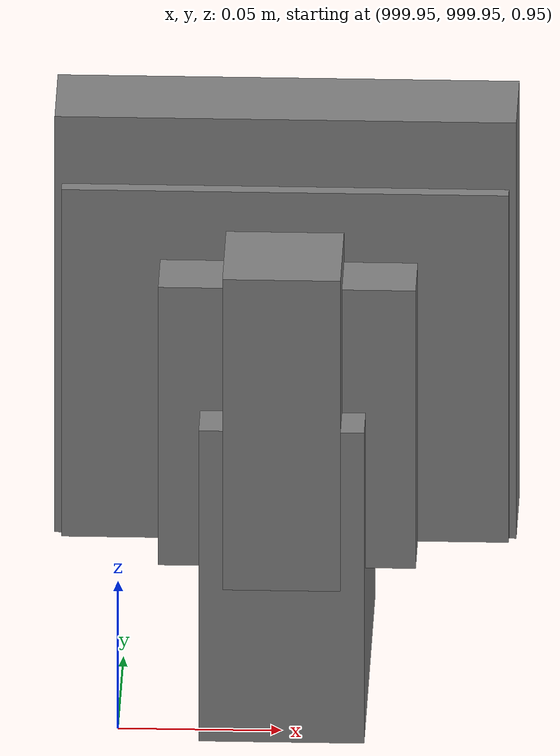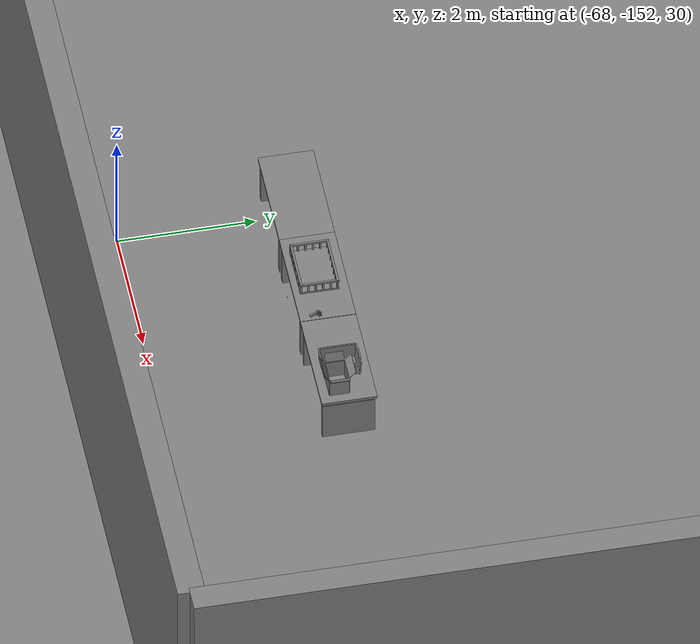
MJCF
<mujoco>
    <option gravity="0.000000000 0.000000000 -9.810000420" timestep="0.0049999999" integrator="implicitfast" density="1.225" viscosity="1.8000001e-05" noslip_iterations="10" iterations="100" sdf_iterations="50">
        <flag multiccd="disable"/>
    </option>
    <size memory="1000M"/>
    <compiler coordinate="local"/>
    <worldbody>
        <light cutoff="30" pos="0 1 1" dir="0 -1 -2"/>
        <light cutoff="30" pos="0 -1 1" dir="0 1 -2"/>
        <body pos="1000.000000000 1000.000000000 1.000000000" euler="0.000000000 0.000000000 180.000000000" name="openloong_gripper_2f85_fix_base_usda_wifi_box">
            <geom contype="1" conaffinity="1" density="1000" type="box" material="" rgba="0.500000000 0.500000000 0.500000000 1.000000000" solimp="0.899999976 0.949999988 0.001000000" friction="1.000000000 0.005000000 0.000100000" solref="0.020000000 1.000000000" margin="0" condim="3" group="0" pos="0.000000000 0.000000000 0.058978677" quat="0.000000000 0.000000047 0.000000000 1.000000000" size="0.068499997 0.018999999 0.059000000" name="openloong_gripper_2f85_fix_base_usda_geom_378EAB6A_A6DD_4539_9376_B859961B1FF5"/>
            <freejoint name="openloong_gripper_2f85_fix_base_usda_wifi_box_joint"/>
            <site size="0.005000000 0.005000000 0.005000000" rgba="0.500000000 0.500000000 0.500000000 1.000000000" pos="0.000000000 0.000000000 0.000000000" quat="0.999961913 0.008726500 0.000000000 0.000000000" group="0" type="sphere" name="openloong_gripper_2f85_fix_base_usda_wifi_boxsite"/>
        </body>
        <body pos="1000.000000000 1000.000000000 1.000000000" euler="0.000000000 0.000000000 180.000000000" name="openloong_gripper_2f85_fix_base_usda_cpu_fan">
            <geom contype="1" conaffinity="1" density="1000" type="box" material="" rgba="0.500000000 0.500000000 0.500000000 1.000000000" solimp="0.899999976 0.949999988 0.001000000" friction="1.000000000 0.005000000 0.000100000" solref="0.020000000 1.000000000" margin="0" condim="3" group="0" pos="0.000000000 0.000000000 0.070034981" quat="0.000000000 0.000000000 0.000000000 1.000000000" size="0.070700005 0.014699999 0.070700005" name="openloong_gripper_2f85_fix_base_usda_geom_B591DF9A_875B_4514_97CA_1BF8CEE3A066"/>
            <freejoint name="openloong_gripper_2f85_fix_base_usda_cpu_fan_joint"/>
            <site size="0.005000000 0.005000000 0.005000000" rgba="0.500000000 0.500000000 0.500000000 1.000000000" pos="0.000000000 0.000000000 0.000000000" quat="0.999961913 0.008726535 0.000000000 0.000000000" group="0" type="sphere" name="openloong_gripper_2f85_fix_base_usda_cpu_fancsite"/>
        </body>
        <body pos="-65.985115051 -149.454925537 31.170112610" euler="-71.971160889 36.025646210 84.493263245" mocap="true" name="spotlight6_SpotLight"/>
        <body pos="1000.000000000 1000.000000000 1.000000000" euler="0.000000000 0.000000000 180.000000000" name="openloong_gripper_2f85_fix_base_usda_battery_01">
            <geom contype="1" conaffinity="1" density="1000" type="box" material="" rgba="0.500000000 0.500000000 0.500000000 1.000000000" solimp="0.899999976 0.949999988 0.001000000" friction="1.000000000 0.005000000 0.000100000" solref="0.020000000 1.000000000" margin="0" condim="3" group="0" pos="-0.011123657 -0.041940309 0.101691343" quat="1.000000000 0.000000000 0.000000000 0.000000000" size="0.010800000 0.003375000 0.004725000" name="openloong_gripper_2f85_fix_base_usda_geom_AD905050_5C70_40C6_97CA_EBA1EEE35EF2"/>
            <geom contype="1" conaffinity="1" density="1000" type="box" material="" rgba="0.500000000 0.500000000 0.500000000 1.000000000" solimp="0.899999976 0.949999988 0.001000000" friction="1.000000000 0.005000000 0.000100000" solref="0.020000000 1.000000000" margin="0" condim="3" group="0" pos="-0.010876465 -0.044247437 0.047066893" quat="0.998702705 -0.050920475 0.000000000 0.000000000" size="0.009450001 0.002700000 0.024975000" name="openloong_gripper_2f85_fix_base_usda_geom_388EBDBB_A0D8_43B1_A4D7_EFA725CD34C0"/>
            <geom contype="1" conaffinity="1" density="1000" type="box" material="" rgba="0.500000000 0.500000000 0.500000000 1.000000000" solimp="0.899999976 0.949999988 0.001000000" friction="1.000000000 0.005000000 0.000100000" solref="0.020000000 1.000000000" margin="0" condim="3" group="0" pos="-0.001235962 -0.000659180 0.047381196" quat="1.000000000 0.000000000 0.000000000 0.000000000" size="0.039420001 0.039150000 0.047250003" name="openloong_gripper_2f85_fix_base_usda_geom_23B53785_40C4_4E03_B1F3_66F4B82495D9"/>
            <geom contype="1" conaffinity="1" density="1000" type="box" material="" rgba="0.500000000 0.500000000 0.500000000 1.000000000" solimp="0.899999976 0.949999988 0.001000000" friction="1.000000000 0.005000000 0.000100000" solref="0.020000000 1.000000000" margin="0" condim="3" group="0" pos="-0.010876465 -0.039138794 0.009851727" quat="1.000000000 0.000000000 0.000000000 0.000000000" size="0.009450001 0.010800000 0.013500000" name="openloong_gripper_2f85_fix_base_usda_geom_BE9AE612_5813_4370_96F6_8089EFB5157B"/>
            <geom contype="1" conaffinity="1" density="1000" type="box" material="" rgba="0.500000000 0.500000000 0.500000000 1.000000000" solimp="0.899999976 0.949999988 0.001000000" friction="1.000000000 0.005000000 0.000100000" solref="0.020000000 1.000000000" margin="0" condim="3" group="0" pos="-0.010876465 -0.041528322 0.071508206" quat="1.000000000 0.000000000 0.000000000 0.000000000" size="0.009450001 0.002700000 0.027000001" name="openloong_gripper_2f85_fix_base_usda_geom_F7F99AEC_FC80_4AE2_9EAF_27E95035B3D3"/>
            <freejoint name="openloong_gripper_2f85_fix_base_usda_battery_01_joint"/>
            <site size="0.005000000 0.005000000 0.005000000" rgba="0.500000000 0.500000000 0.500000000 1.000000000" pos="0.000000000 0.000000000 0.000000000" quat="0.999961913 0.008726500 0.000000000 0.000000000" group="0" type="sphere" name="openloong_gripper_2f85_fix_base_usda_battery_01site"/>
        </body>
        <body pos="-66.194091797 -149.123214722 31.167327881" euler="-144.027236938 -26.858242035 96.428688049" mocap="true" name="spotlight3_SpotLight"/>
        <body pos="1000.000000000 1000.000000000 1.000000000" euler="0.000011953 0.000005123 -179.999984741" name="openloong_gripper_2f85_fix_base_usda_intel_box">
            <geom contype="1" conaffinity="1" density="1000" type="box" material="" rgba="0.500000000 0.500000000 0.500000000 1.000000000" solimp="0.899999976 0.949999988 0.001000000" friction="1.000000000 0.005000000 0.000100000" solref="0.020000000 1.000000000" margin="0" condim="3" group="0" pos="0.000000000 -0.000067139 0.000082284" quat="0.707106709 0.000000225 0.000000253 0.707106650" size="0.052800003 0.025300000 0.052800003" name="openloong_gripper_2f85_fix_base_usda_geom_894A9DA7_6670_4193_902E_45F7A6368EF3"/>
            <freejoint name="openloong_gripper_2f85_fix_base_usda_intel_box_joint"/>
            <site size="0.005000000 0.005000000 0.005000000" rgba="0.500000000 0.500000000 0.500000000 1.000000000" pos="0.000000000 0.000000000 0.000000000" quat="0.999961913 0.008726500 0.000000000 0.000000000" group="0" type="sphere" name="openloong_gripper_2f85_fix_base_usda_intel_boxsite"/>
        </body>
        <body pos="1000.000000000 999.999938965 1.000000000" euler="0.000000000 0.000000000 180.000000000" name="openloong_gripper_2f85_fix_base_usda_intelcore_i5">
            <geom contype="1" conaffinity="1" density="1000" type="box" material="" rgba="0.500000000 0.500000000 0.500000000 1.000000000" solimp="0.899999976 0.949999988 0.001000000" friction="1.000000000 0.005000000 0.000100000" solref="0.020000000 1.000000000" margin="0" condim="3" group="0" pos="0.000000000 0.000000000 0.051722717" quat="0.707106709 0.000000000 0.000000000 -0.707106769" size="0.052800000 0.018080002 0.052800000" name="openloong_gripper_2f85_fix_base_usda_geom_4BB7264B_5C89_4D60_A896_1D9D11180438"/>
            <freejoint name="openloong_gripper_2f85_fix_base_usda_intelcore_i5_joint"/>
            <site size="0.005000000 0.005000000 0.005000000" rgba="0.500000000 0.500000000 0.500000000 1.000000000" pos="0.000000000 0.000000000 0.000000000" quat="0.999961913 0.008726534 0.000000000 0.000000000" group="0" type="sphere" name="openloong_gripper_2f85_fix_base_usda_intelcore_i5site"/>
        </body>
        <body pos="-65.956672668 -148.960571289 31.166051865" euler="-170.927917480 10.482763290 -54.268836975" mocap="true" name="spotlight4_SpotLight"/>
        <body pos="-64.866622925 -149.383972168 30.183746338" euler="89.999984741 89.999946594 0.000000000" name="openloong_gripper_2f85_fix_base_usda_bluebox_01">
            <geom contype="1" conaffinity="1" density="1000" type="box" material="" rgba="0.500000000 0.500000000 0.500000000 1.000000000" solimp="0.899999976 0.949999988 0.001000000" friction="1.000000000 0.005000000 0.000100000" solref="0.020000000 1.000000000" margin="0" condim="3" group="0" pos="0.276580811 0.187225342 0.000068665" quat="0.707106948 0.000077471 0.707106352 0.000077486" size="0.100000001 0.057999998 0.010000000" name="openloong_gripper_2f85_fix_base_usda_geom_ADE6DED6_1F5E_4805_8632_4F923DA7BF58"/>
            <geom contype="1" conaffinity="1" density="1000" type="box" material="" rgba="0.500000000 0.500000000 0.500000000 1.000000000" solimp="0.899999976 0.949999988 0.001000000" friction="1.000000000 0.005000000 0.000100000" solref="0.020000000 1.000000000" margin="0" condim="3" group="0" pos="0.000000000 0.002883911 0.000000000" quat="0.999999881 0.000000000 0.000000000 0.000000000" size="0.254000008 0.003000000 0.172000006" name="openloong_gripper_2f85_fix_base_usda_geom_1990C536_DB16_43AB_A7BD_A4E2C9B9A56E"/>
            <geom contype="1" conaffinity="1" density="1000" type="box" material="" rgba="0.500000000 0.500000000 0.500000000 1.000000000" solimp="0.899999976 0.949999988 0.001000000" friction="1.000000000 0.005000000 0.000100000" solref="0.020000000 1.000000000" margin="0" condim="3" group="0" pos="0.000000000 0.124874115 0.173484802" quat="0.999796331 0.020176515 -0.000000015 0.000000030" size="0.259999990 0.119999997 0.007000000" name="openloong_gripper_2f85_fix_base_usda_geom_12F92C8E_FF05_44C4_9D64_98037A6B6739"/>
            <geom contype="1" conaffinity="1" density="1000" type="box" material="" rgba="0.500000000 0.500000000 0.500000000 1.000000000" solimp="0.899999976 0.949999988 0.001000000" friction="1.000000000 0.005000000 0.000100000" solref="0.020000000 1.000000000" margin="0" condim="3" group="0" pos="0.000000000 0.124874115 -0.173469543" quat="0.999796331 -0.020176545 -0.000000015 0.000000000" size="0.259999990 0.119999997 0.007000000" name="openloong_gripper_2f85_fix_base_usda_geom_A31CDEB2_1AEE_4A22_85A2_F5AA4336F6DA"/>
            <geom contype="1" conaffinity="1" density="1000" type="box" material="" rgba="0.500000000 0.500000000 0.500000000 1.000000000" solimp="0.899999976 0.949999988 0.001000000" friction="1.000000000 0.005000000 0.000100000" solref="0.020000000 1.000000000" margin="0" condim="3" group="0" pos="0.000000000 0.214008331 0.188980103" quat="0.999912977 0.013176724 0.000000015 0.000000000" size="0.259999990 0.029999999 0.012500000" name="openloong_gripper_2f85_fix_base_usda_geom_387D7595_E1C3_44FD_823D_DD77BF0BD0C7"/>
            <geom contype="1" conaffinity="1" density="1000" type="box" material="" rgba="0.500000000 0.500000000 0.500000000 1.000000000" solimp="0.899999976 0.949999988 0.001000000" friction="1.000000000 0.005000000 0.000100000" solref="0.020000000 1.000000000" margin="0" condim="3" group="0" pos="-0.258361816 0.125289917 0.001876831" quat="0.702796936 -0.020792112 0.710783124 0.020769298" size="0.189999998 0.119999997 0.009000000" name="openloong_gripper_2f85_fix_base_usda_geom_C1CDBEB8_8D28_434B_9708_EF63439C6E28"/>
            <geom contype="1" conaffinity="1" density="1000" type="box" material="" rgba="0.500000000 0.500000000 0.500000000 1.000000000" solimp="0.899999976 0.949999988 0.001000000" friction="1.000000000 0.005000000 0.000100000" solref="0.020000000 1.000000000" margin="0" condim="3" group="0" pos="0.000000000 0.214008331 -0.188980103" quat="0.999912977 -0.013176769 0.000000030 0.000000015" size="0.259999990 0.029999999 0.012500000" name="openloong_gripper_2f85_fix_base_usda_geom_8D030BBB_D107_4CEE_AA4A_AD64C974803B"/>
            <geom contype="1" conaffinity="1" density="1000" type="box" material="" rgba="0.500000000 0.500000000 0.500000000 1.000000000" solimp="0.899999976 0.949999988 0.001000000" friction="1.000000000 0.005000000 0.000100000" solref="0.020000000 1.000000000" margin="0" condim="3" group="0" pos="-0.276611328 0.187225342 0.000068665" quat="0.707106650 0.000077441 0.707106709 0.000077456" size="0.100000001 0.057999998 0.010000000" name="openloong_gripper_2f85_fix_base_usda_geom_CF77F506_F6EF_4369_B2FB_C126158104DC"/>
            <geom contype="1" conaffinity="1" density="1000" type="box" material="" rgba="0.500000000 0.500000000 0.500000000 1.000000000" solimp="0.899999976 0.949999988 0.001000000" friction="1.000000000 0.005000000 0.000100000" solref="0.020000000 1.000000000" margin="0" condim="3" group="0" pos="0.258331299 0.125289917 0.001876831" quat="0.702851415 0.018856421 0.710823774 -0.019329369" size="0.189999998 0.119999997 0.009000000" name="openloong_gripper_2f85_fix_base_usda_geom_D4256BA7_859C_4239_9D3A_59C485C433CF"/>
            <freejoint name="openloong_gripper_2f85_fix_base_usda_bluebox_01_joint"/>
            <site size="0.005000000 0.005000000 0.005000000" rgba="0.500000000 0.500000000 0.500000000 1.000000000" pos="0.000000000 0.000000000 0.000000000" quat="0.999961913 0.008726534 0.000000000 0.000000000" group="0" type="sphere" name="openloong_gripper_2f85_fix_base_usda_bluebox_01site"/>
        </body>
        <body pos="-64.496299744 -149.491867065 30.235729218" euler="0.000000000 0.000000000 89.999946594" name="openloong_gripper_2f85_fix_base_usda_cardboardbox_01">
            <geom contype="1" conaffinity="1" density="1000" type="box" material="" rgba="0.500000000 0.500000000 0.500000000 1.000000000" solimp="0.899999976 0.949999988 0.001000000" friction="1.000000000 0.005000000 0.000100000" solref="0.020000000 1.000000000" margin="0" condim="3" group="0" pos="-0.003166199 -0.004086494 0.005052090" quat="1.000000000 0.000000000 0.000000000 0.000000000" size="0.142499998 0.177500010 0.005000000" name="openloong_gripper_2f85_fix_base_usda_geom_82B125E8_DC32_4A9B_A834_52C7869673D6"/>
            <geom contype="1" conaffinity="1" density="1000" type="box" material="" rgba="0.500000000 0.500000000 0.500000000 1.000000000" solimp="0.899999976 0.949999988 0.001000000" friction="1.000000000 0.005000000 0.000100000" solref="0.020000000 1.000000000" margin="0" condim="3" group="0" pos="-0.003166199 0.170316696 0.150570869" quat="1.000000000 0.000000000 0.000000000 0.000000000" size="0.142499998 0.005000000 0.149999991" name="openloong_gripper_2f85_fix_base_usda_geom_7745D962_DC6E_4730_970C_79A89136AA69"/>
            <geom contype="1" conaffinity="1" density="1000" type="box" material="" rgba="0.500000000 0.500000000 0.500000000 1.000000000" solimp="0.899999976 0.949999988 0.001000000" friction="1.000000000 0.005000000 0.000100000" solref="0.020000000 1.000000000" margin="0" condim="3" group="0" pos="-0.147399902 -0.005307198 0.150570869" quat="1.000000000 0.000000000 0.000000000 0.000000000" size="0.005000000 0.177500010 0.149999991" name="openloong_gripper_2f85_fix_base_usda_geom_631CFEC6_8938_487C_BBDD_50F624C4C94F"/>
            <geom contype="1" conaffinity="1" density="1000" type="box" material="" rgba="0.500000000 0.500000000 0.500000000 1.000000000" solimp="0.899999976 0.949999988 0.001000000" friction="1.000000000 0.005000000 0.000100000" solref="0.020000000 1.000000000" margin="0" condim="3" group="0" pos="0.140275955 -0.005307198 0.150570869" quat="1.000000000 0.000000000 0.000000000 0.000000000" size="0.005000000 0.177500010 0.149999991" name="openloong_gripper_2f85_fix_base_usda_geom_DBA92276_FC39_48F5_85D8_9FD88ECFFB65"/>
            <geom contype="1" conaffinity="1" density="1000" type="box" material="" rgba="0.500000000 0.500000000 0.500000000 1.000000000" solimp="0.899999976 0.949999988 0.001000000" friction="1.000000000 0.005000000 0.000100000" solref="0.020000000 1.000000000" margin="0" condim="3" group="0" pos="-0.003166199 -0.181550980 0.150570869" quat="1.000000000 0.000000000 0.000000000 0.000000000" size="0.142499998 0.005000000 0.149999991" name="openloong_gripper_2f85_fix_base_usda_geom_D68EA041_A511_4C04_BC0D_7FC056579FCB"/>
            <freejoint name="openloong_gripper_2f85_fix_base_usda_cardboardbox_01_joint"/>
            <site size="0.005000000 0.005000000 0.005000000" rgba="0.500000000 0.500000000 0.500000000 1.000000000" pos="0.000000000 0.000000000 0.000000000" quat="0.999961913 0.008726535 0.000000000 0.000000000" group="0" type="sphere" name="openloong_gripper_2f85_fix_base_usda_site_6D88B94C_DC70_47A1_80CF_563C029DB3B7"/>
            <body pos="0.139160156 -0.004048347 0.301930904" euler="-179.999954224 49.383502960 179.999954224" name="openloong_gripper_2f85_fix_base_usda_A1_006">
                <geom contype="1" conaffinity="1" density="1000" type="box" material="" rgba="0.500000000 0.500000000 0.500000000 1.000000000" solimp="0.899999976 0.949999988 0.001000000" friction="1.000000000 0.005000000 0.000100000" solref="0.020000000 1.000000000" margin="0" condim="3" group="0" pos="-0.071587563 0.000009537 0.001745224" quat="0.999999881 0.000000000 0.000000000 0.000000000" size="0.071249999 0.179999992 0.002500000" name="openloong_gripper_2f85_fix_base_usda_geom_614C5403_7A25_40F6_9BE0_B93ABE25F303"/>
                <joint armature="0" stiffness="0.07" damping="0.0099999998" axis="0.000000 1.000000 0.000000" type="hinge" name="openloong_gripper_2f85_fix_base_usda_A1_006"/>
            </body>
            <body pos="-0.145902634 -0.004086494 0.301938057" euler="-180.000000000 -60.000011444 -180.000000000" name="openloong_gripper_2f85_fix_base_usda_A2_006">
                <geom contype="1" conaffinity="1" density="1000" type="box" material="" rgba="0.500000000 0.500000000 0.500000000 1.000000000" solimp="0.899999976 0.949999988 0.001000000" friction="1.000000000 0.005000000 0.000100000" solref="0.020000000 1.000000000" margin="0" condim="3" group="0" pos="0.071268082 0.000009537 0.002717972" quat="0.000002921 0.000000000 -0.000000030 0.999999881" size="0.071249999 0.179999992 0.002500000" name="openloong_gripper_2f85_fix_base_usda_geom_2D61FC97_D1B7_43E2_932C_ACDD7A33ACFA"/>
                <joint armature="0" stiffness="0.07" damping="0.0099999998" axis="0.000000 1.000000 0.000000" type="hinge" name="openloong_gripper_2f85_fix_base_usda_A2_006"/>
            </body>
            <body pos="-0.003385544 0.175991058 0.301930904" euler="-125.858116150 -0.000004561 0.000002331" name="openloong_gripper_2f85_fix_base_usda_B2_006">
                <geom contype="1" conaffinity="1" density="1000" type="box" material="" rgba="0.500000000 0.500000000 0.500000000 1.000000000" solimp="0.899999976 0.949999988 0.001000000" friction="1.000000000 0.005000000 0.000100000" solref="0.020000000 1.000000000" margin="0" condim="3" group="0" pos="0.000009537 -0.070939064 -0.002470016" quat="0.999614120 0.027776197 -0.000000015 0.000000030" size="0.137500003 0.064999998 0.005000000" name="openloong_gripper_2f85_fix_base_usda_geom_E657FDBC_585E_42D3_BA18_E6183D10DAA3"/>
                <joint armature="0" stiffness="0.07" damping="0.0099999998" axis="1.000000 0.000000 0.000000" type="hinge" name="openloong_gripper_2f85_fix_base_usda_B2_006"/>
            </body>
            <body pos="-0.003385544 -0.184140205 0.301938057" euler="147.805557251 0.000000000 0.000000000" name="openloong_gripper_2f85_fix_base_usda_B1_006">
                <geom contype="1" conaffinity="1" density="1000" type="box" material="" rgba="0.500000000 0.500000000 0.500000000 1.000000000" solimp="0.899999976 0.949999988 0.001000000" friction="1.000000000 0.005000000 0.000100000" solref="0.020000000 1.000000000" margin="0" condim="3" group="0" pos="-0.000028610 0.070202351 -0.002703667" quat="0.999614179 -0.027776167 0.000000000 0.000000000" size="0.137500003 0.064999998 0.005000000" name="openloong_gripper_2f85_fix_base_usda_geom_5CB576F2_D60B_4B75_9F57_D55FE634DB09"/>
                <joint armature="0" stiffness="0.07" damping="0.0099999998" axis="1.000000 0.000000 0.000000" type="hinge" name="openloong_gripper_2f85_fix_base_usda_B1_006"/>
            </body>
        </body>
        <body pos="-65.882858276 -149.481979370 30.229999542" euler="-64.487716675 0.000000000 0.000000000" name="openloong_gripper_2f85_fix_base_usda_Barcode">
            <geom contype="1" conaffinity="1" density="1000" type="box" material="" rgba="0.500000000 0.500000000 0.500000000 1.000000000" solimp="0.899999976 0.949999988 0.001000000" friction="1.000000000 0.005000000 0.000100000" solref="0.020000000 1.000000000" margin="0" condim="3" group="0" pos="0.000000000 0.013038635 0.001419067" quat="0.000000000 0.000000000 0.000000000 1.000000119" size="0.034000002 0.010000000 0.017999999" name="openloong_gripper_2f85_fix_base_usda_geom_D933B608_74FD_4D2F_B624_9A2DB1B8BDE0"/>
            <geom contype="1" conaffinity="1" density="1000" type="box" material="" rgba="0.500000000 0.500000000 0.500000000 1.000000000" solimp="0.899999976 0.949999988 0.001000000" friction="1.000000000 0.005000000 0.000100000" solref="0.020000000 1.000000000" margin="0" condim="3" group="0" pos="0.000000000 -0.035301208 -0.007095337" quat="0.000000000 0.000000000 -0.043619365 0.999048233" size="0.028999999 0.010000000 0.020000000" name="openloong_gripper_2f85_fix_base_usda_geom_FB6C4AA8_6929_4B04_87FB_34AF349D0C26"/>
            <geom contype="1" conaffinity="1" density="1000" type="box" material="" rgba="0.500000000 0.500000000 0.500000000 1.000000000" solimp="0.899999976 0.949999988 0.001000000" friction="1.000000000 0.005000000 0.000100000" solref="0.020000000 1.000000000" margin="0" condim="3" group="0" pos="0.000000000 -0.043411255 -0.011749268" quat="0.922262907 0.386563420 0.000000000 0.000000000" size="0.026000001 0.010000000 0.020000000" name="openloong_gripper_2f85_fix_base_usda_geom_85B7A0DB_5921_4780_8607_FDCF4686BC8F"/>
            <geom contype="1" conaffinity="1" density="1000" type="box" material="" rgba="0.500000000 0.500000000 0.500000000 1.000000000" solimp="0.899999976 0.949999988 0.001000000" friction="1.000000000 0.005000000 0.000100000" solref="0.020000000 1.000000000" margin="0" condim="3" group="0" pos="0.000000000 -0.016967773 -0.031860352" quat="0.000000000 0.000000000 0.000000000 1.000000119" size="0.008000000 0.010000000 0.013000000" name="openloong_gripper_2f85_fix_base_usda_geom_7494C0AA_94FF_4416_A701_87275BC4FCB7"/>
            <geom contype="1" conaffinity="1" density="1000" type="box" material="" rgba="0.500000000 0.500000000 0.500000000 1.000000000" solimp="0.899999976 0.949999988 0.001000000" friction="1.000000000 0.005000000 0.000100000" solref="0.020000000 1.000000000" margin="0" condim="3" group="0" pos="0.000000000 -0.001869202 0.000312805" quat="0.953716993 0.300705761 0.000000000 0.000000000" size="0.032000002 0.010000000 0.018999999" name="openloong_gripper_2f85_fix_base_usda_geom_5C444F94_9077_461B_879A_6FD90AE26376"/>
            <geom contype="1" conaffinity="1" density="1000" type="box" material="" rgba="0.500000000 0.500000000 0.500000000 1.000000000" solimp="0.899999976 0.949999988 0.001000000" friction="1.000000000 0.005000000 0.000100000" solref="0.020000000 1.000000000" margin="0" condim="3" group="0" pos="0.000000000 -0.019531250 -0.003173828" quat="0.953716993 0.300705761 0.000000000 0.000000000" size="0.030999999 0.010000000 0.020000000" name="openloong_gripper_2f85_fix_base_usda_geom_2C3BCCD9_163F_4F2F_B7A2_4E4F0B0BF7B7"/>
            <geom contype="1" conaffinity="1" density="1000" type="box" material="" rgba="0.500000000 0.500000000 0.500000000 1.000000000" solimp="0.899999976 0.949999988 0.001000000" friction="1.000000000 0.005000000 0.000100000" solref="0.020000000 1.000000000" margin="0" condim="3" group="0" pos="0.000000000 -0.035301208 -0.007095337" quat="0.953716993 0.300705761 0.000000000 0.000000000" size="0.028999999 0.010000000 0.020000000" name="openloong_gripper_2f85_fix_base_usda_geom_E3CE4406_7430_4384_ADBA_73C20F3C570A"/>
            <geom contype="1" conaffinity="1" density="1000" type="box" material="" rgba="0.500000000 0.500000000 0.500000000 1.000000000" solimp="0.899999976 0.949999988 0.001000000" friction="1.000000000 0.005000000 0.000100000" solref="0.020000000 1.000000000" margin="0" condim="3" group="0" pos="0.000000000 -0.042617798 -0.071121216" quat="0.000000000 0.000000000 0.000000000 1.000000119" size="0.013000000 0.021000000 0.059999999" name="openloong_gripper_2f85_fix_base_usda_geom_964B814C_1279_45E1_9FFB_5B7F856BF6C3"/>
            <freejoint name="openloong_gripper_2f85_fix_base_usda_Barcode_joint"/>
            <site size="0.005000000 0.005000000 0.005000000" rgba="0.500000000 0.500000000 0.500000000 1.000000000" pos="0.000000000 0.000000000 0.000000000" quat="1.000000000 0.000000000 0.000000000 0.000000000" group="0" type="sphere" name="openloong_gripper_2f85_fix_base_usda_Barcode_site"/>
        </body>
        <body pos="-66.745018005 -149.392349243 30.184000015" euler="0.000000000 0.000000000 89.999946594" name="[22331944044354]_Basket_01">
            <geom contype="1" conaffinity="1" density="1000" type="box" material="" rgba="0.500000000 0.500000000 0.500000000 1.000000000" solimp="0.899999976 0.949999988 0.001000000" friction="1.000000000 0.005000000 0.000100000" solref="0.020000000 1.000000000" margin="0" condim="3" group="0" pos="-0.052425385 0.389207840 0.089787483" quat="0.707107008 0.000000000 0.000000000 0.707106411" size="0.014249999 0.014249999 0.059999999" name="[22331944044354]_geom_DBBC9CC8_F4E2_46E0_88D2_093F3DF3098A"/>
            <geom contype="1" conaffinity="1" density="1000" type="box" material="" rgba="0.500000000 0.500000000 0.500000000 1.000000000" solimp="0.899999976 0.949999988 0.001000000" friction="1.000000000 0.005000000 0.000100000" solref="0.020000000 1.000000000" margin="0" condim="3" group="0" pos="0.264015198 -0.133043289 0.089787483" quat="0.707107008 0.000000000 0.000000000 0.707106411" size="0.014249999 0.014249999 0.059999999" name="[22331944044354]_geom_1C58DF71_8517_4461_93FD_B0ED8A807C73"/>
            <geom contype="1" conaffinity="1" density="1000" type="box" material="" rgba="0.500000000 0.500000000 0.500000000 1.000000000" solimp="0.899999976 0.949999988 0.001000000" friction="1.000000000 0.005000000 0.000100000" solref="0.020000000 1.000000000" margin="0" condim="3" group="0" pos="-0.264015198 -0.265548706 0.089793205" quat="0.707107008 0.000000000 0.000000000 0.707106411" size="0.014249999 0.014249999 0.059999999" name="[22331944044354]_geom_A864090F_D25C_404E_8DBF_ECCFD7F908DD"/>
            <geom contype="1" conaffinity="1" density="1000" type="box" material="" rgba="0.500000000 0.500000000 0.500000000 1.000000000" solimp="0.899999976 0.949999988 0.001000000" friction="1.000000000 0.005000000 0.000100000" solref="0.020000000 1.000000000" margin="0" condim="3" group="0" pos="-0.160263062 -0.389322281 0.089793205" quat="0.707107008 0.000000000 0.000000000 0.707106411" size="0.014249999 0.014249999 0.059999999" name="[22331944044354]_geom_26DA0DE2_9C60_422C_A0B5_BA435896504E"/>
            <geom contype="1" conaffinity="1" density="1000" type="box" material="" rgba="0.500000000 0.500000000 0.500000000 1.000000000" solimp="0.899999976 0.949999988 0.001000000" friction="1.000000000 0.005000000 0.000100000" solref="0.020000000 1.000000000" margin="0" condim="3" group="0" pos="0.162265778 -0.389322281 0.089787483" quat="0.707107008 0.000000000 0.000000000 0.707106411" size="0.014249999 0.014249999 0.059999999" name="[22331944044354]_geom_80AFE6EB_BC78_4C71_82D0_12BF4D82899C"/>
            <geom contype="1" conaffinity="1" density="1000" type="box" material="" rgba="0.500000000 0.500000000 0.500000000 1.000000000" solimp="0.899999976 0.949999988 0.001000000" friction="1.000000000 0.005000000 0.000100000" solref="0.020000000 1.000000000" margin="0" condim="3" group="0" pos="0.264015198 0.389207840 0.089787483" quat="0.707107008 0.000000000 0.000000000 0.707106411" size="0.014249999 0.014249999 0.059999999" name="[22331944044354]_geom_3DE5E7AE_6F18_4112_BE76_165BAF23CDBE"/>
            <geom contype="1" conaffinity="1" density="1000" type="box" material="" rgba="0.500000000 0.500000000 0.500000000 1.000000000" solimp="0.899999976 0.949999988 0.001000000" friction="1.000000000 0.005000000 0.000100000" solref="0.020000000 1.000000000" margin="0" condim="3" group="0" pos="-0.264015198 -0.133043289 0.089793205" quat="0.707107008 0.000000000 0.000000000 0.707106411" size="0.014249999 0.014249999 0.059999999" name="[22331944044354]_geom_7150680D_6DD1_4BCD_A940_EE02D1D7833E"/>
            <geom contype="1" conaffinity="1" density="1000" type="box" material="" rgba="0.500000000 0.500000000 0.500000000 1.000000000" solimp="0.899999976 0.949999988 0.001000000" friction="1.000000000 0.005000000 0.000100000" solref="0.020000000 1.000000000" margin="0" condim="3" group="0" pos="-0.264026642 0.269256592 0.089793205" quat="0.707107008 0.000000000 0.000000000 0.707106411" size="0.014249999 0.014249999 0.059999999" name="[22331944044354]_geom_EB13DFA9_1861_49F9_AEBE_697EE30476EF"/>
            <geom contype="1" conaffinity="1" density="1000" type="box" material="" rgba="0.500000000 0.500000000 0.500000000 1.000000000" solimp="0.899999976 0.949999988 0.001000000" friction="1.000000000 0.005000000 0.000100000" solref="0.020000000 1.000000000" margin="0" condim="3" group="0" pos="0.054462433 0.389207840 0.089787483" quat="0.707107008 0.000000000 0.000000000 0.707106411" size="0.014249999 0.014249999 0.059999999" name="[22331944044354]_geom_DCC86051_17FF_4539_AA76_9B2909D2AAB6"/>
            <geom contype="1" conaffinity="1" density="1000" type="box" material="" rgba="0.500000000 0.500000000 0.500000000 1.000000000" solimp="0.899999976 0.949999988 0.001000000" friction="1.000000000 0.005000000 0.000100000" solref="0.020000000 1.000000000" margin="0" condim="3" group="0" pos="0.054462433 -0.389322281 0.089787483" quat="0.707107008 0.000000000 0.000000000 0.707106411" size="0.014249999 0.014249999 0.059999999" name="[22331944044354]_geom_B4901E60_A50B_4632_AC28_9EC2110D807C"/>
            <geom contype="1" conaffinity="1" density="1000" type="box" material="" rgba="0.500000000 0.500000000 0.500000000 1.000000000" solimp="0.899999976 0.949999988 0.001000000" friction="1.000000000 0.005000000 0.000100000" solref="0.020000000 1.000000000" margin="0" condim="3" group="0" pos="0.264015198 0.269256592 0.089793205" quat="0.707107008 0.000000000 0.000000000 0.707106411" size="0.014249999 0.014249999 0.059999999" name="[22331944044354]_geom_59126867_509D_4379_85DB_8D1ACDC5E145"/>
            <geom contype="1" conaffinity="1" density="1000" type="box" material="" rgba="0.500000000 0.500000000 0.500000000 1.000000000" solimp="0.899999976 0.949999988 0.001000000" friction="1.000000000 0.005000000 0.000100000" solref="0.020000000 1.000000000" margin="0" condim="3" group="0" pos="0.264015198 -0.389322281 0.089787483" quat="0.707107008 0.000000000 0.000000000 0.707106411" size="0.014249999 0.014249999 0.059999999" name="[22331944044354]_geom_9196BE0F_92EA_45EA_B0DF_2ECB202AE719"/>
            <geom contype="1" conaffinity="1" density="1000" type="box" material="" rgba="0.500000000 0.500000000 0.500000000 1.000000000" solimp="0.899999976 0.949999988 0.001000000" friction="1.000000000 0.005000000 0.000100000" solref="0.020000000 1.000000000" margin="0" condim="3" group="0" pos="0.000000000 0.000000000 0.015998840" quat="0.707107008 0.000000000 0.000000000 0.707106411" size="0.403499991 0.279000014 0.015750000" name="[22331944044354]_geom_81F2202E_9F1D_4822_809C_082F753DB57F"/>
            <geom contype="1" conaffinity="1" density="1000" type="box" material="" rgba="0.500000000 0.500000000 0.500000000 1.000000000" solimp="0.899999976 0.949999988 0.001000000" friction="1.000000000 0.005000000 0.000100000" solref="0.020000000 1.000000000" margin="0" condim="3" group="0" pos="0.000000000 -0.389476776 0.163619041" quat="0.707107008 0.000000000 0.000000000 0.707106411" size="0.015000000 0.277500004 0.015750000" name="[22331944044354]_geom_56296DAF_6E46_49BA_BC8E_6DEDE0CA0AA4"/>
            <geom contype="1" conaffinity="1" density="1000" type="box" material="" rgba="0.500000000 0.500000000 0.500000000 1.000000000" solimp="0.899999976 0.949999988 0.001000000" friction="1.000000000 0.005000000 0.000100000" solref="0.020000000 1.000000000" margin="0" condim="3" group="0" pos="0.162265778 0.389207840 0.089787483" quat="0.707107008 0.000000000 0.000000000 0.707106411" size="0.014249999 0.014249999 0.059999999" name="[22331944044354]_geom_19DE2CD1_17F4_478A_BE1C_107CBCE44BF8"/>
            <geom contype="1" conaffinity="1" density="1000" type="box" material="" rgba="0.500000000 0.500000000 0.500000000 1.000000000" solimp="0.899999976 0.949999988 0.001000000" friction="1.000000000 0.005000000 0.000100000" solref="0.020000000 1.000000000" margin="0" condim="3" group="0" pos="0.000000000 0.389471054 0.163619041" quat="0.707107008 0.000000000 0.000000000 0.707106411" size="0.015000000 0.277500004 0.015750000" name="[22331944044354]_geom_809D4F14_7DB1_40D9_BD48_22093691F760"/>
            <geom contype="1" conaffinity="1" density="1000" type="box" material="" rgba="0.500000000 0.500000000 0.500000000 1.000000000" solimp="0.899999976 0.949999988 0.001000000" friction="1.000000000 0.005000000 0.000100000" solref="0.020000000 1.000000000" margin="0" condim="3" group="0" pos="-0.263511658 0.000000000 0.163619041" quat="0.707107008 0.000000000 0.000000000 0.707106411" size="0.403499991 0.015000000 0.015750000" name="[22331944044354]_geom_3FDF9100_F852_49FC_A1E5_3FFEDCD55742"/>
            <geom contype="1" conaffinity="1" density="1000" type="box" material="" rgba="0.500000000 0.500000000 0.500000000 1.000000000" solimp="0.899999976 0.949999988 0.001000000" friction="1.000000000 0.005000000 0.000100000" solref="0.020000000 1.000000000" margin="0" condim="3" group="0" pos="-0.264015198 0.141334534 0.089793205" quat="0.707107008 0.000000000 0.000000000 0.707106411" size="0.014249999 0.014249999 0.059999999" name="[22331944044354]_geom_942A8C0E_6A78_4C4A_A6CF_7C31D040178B"/>
            <geom contype="1" conaffinity="1" density="1000" type="box" material="" rgba="0.500000000 0.500000000 0.500000000 1.000000000" solimp="0.899999976 0.949999988 0.001000000" friction="1.000000000 0.005000000 0.000100000" solref="0.020000000 1.000000000" margin="0" condim="3" group="0" pos="0.264015198 -0.265548706 0.089787483" quat="0.707107008 0.000000000 0.000000000 0.707106411" size="0.014249999 0.014249999 0.059999999" name="[22331944044354]_geom_1DAF3DC0_83FF_41C7_892A_6C87EE09FF82"/>
            <geom contype="1" conaffinity="1" density="1000" type="box" material="" rgba="0.500000000 0.500000000 0.500000000 1.000000000" solimp="0.899999976 0.949999988 0.001000000" friction="1.000000000 0.005000000 0.000100000" solref="0.020000000 1.000000000" margin="0" condim="3" group="0" pos="-0.160263062 0.389207840 0.089787483" quat="0.707107008 0.000000000 0.000000000 0.707106411" size="0.014249999 0.014249999 0.059999999" name="[22331944044354]_geom_62330117_F590_4763_99DF_A8C001A527F1"/>
            <geom contype="1" conaffinity="1" density="1000" type="box" material="" rgba="0.500000000 0.500000000 0.500000000 1.000000000" solimp="0.899999976 0.949999988 0.001000000" friction="1.000000000 0.005000000 0.000100000" solref="0.020000000 1.000000000" margin="0" condim="3" group="0" pos="-0.052425385 -0.389322281 0.089787483" quat="0.707107008 0.000000000 0.000000000 0.707106411" size="0.014249999 0.014249999 0.059999999" name="[22331944044354]_geom_0422A5B3_22F6_4902_A928_B4B3E0413B7B"/>
            <geom contype="1" conaffinity="1" density="1000" type="box" material="" rgba="0.500000000 0.500000000 0.500000000 1.000000000" solimp="0.899999976 0.949999988 0.001000000" friction="1.000000000 0.005000000 0.000100000" solref="0.020000000 1.000000000" margin="0" condim="3" group="0" pos="-0.264026642 -0.389322281 0.089793205" quat="0.707107008 0.000000000 0.000000000 0.707106411" size="0.014249999 0.014249999 0.059999999" name="[22331944044354]_geom_AD88AC33_03D3_4810_B21D_3FB0751C4769"/>
            <geom contype="1" conaffinity="1" density="1000" type="box" material="" rgba="0.500000000 0.500000000 0.500000000 1.000000000" solimp="0.899999976 0.949999988 0.001000000" friction="1.000000000 0.005000000 0.000100000" solref="0.020000000 1.000000000" margin="0" condim="3" group="0" pos="0.264015198 0.141334534 0.089787483" quat="0.707107008 0.000000000 0.000000000 0.707106411" size="0.014249999 0.014249999 0.059999999" name="[22331944044354]_geom_55E632AE_9131_473C_9EB1_F51F41C4A6E5"/>
            <geom contype="1" conaffinity="1" density="1000" type="box" material="" rgba="0.500000000 0.500000000 0.500000000 1.000000000" solimp="0.899999976 0.949999988 0.001000000" friction="1.000000000 0.005000000 0.000100000" solref="0.020000000 1.000000000" margin="0" condim="3" group="0" pos="-0.264015198 0.389207840 0.089793205" quat="0.707107008 0.000000000 0.000000000 0.707106411" size="0.014249999 0.014249999 0.059999999" name="[22331944044354]_geom_6C37954A_B60F_48A4_BD26_E78C4BDE9A93"/>
            <geom contype="1" conaffinity="1" density="1000" type="box" material="" rgba="0.500000000 0.500000000 0.500000000 1.000000000" solimp="0.899999976 0.949999988 0.001000000" friction="1.000000000 0.005000000 0.000100000" solref="0.020000000 1.000000000" margin="0" condim="3" group="0" pos="0.264015198 0.004480362 0.089787483" quat="0.707107008 0.000000000 0.000000000 0.707106411" size="0.014249999 0.014249999 0.059999999" name="[22331944044354]_geom_2685E269_BC28_4754_A501_6765520ED522"/>
            <geom contype="1" conaffinity="1" density="1000" type="box" material="" rgba="0.500000000 0.500000000 0.500000000 1.000000000" solimp="0.899999976 0.949999988 0.001000000" friction="1.000000000 0.005000000 0.000100000" solref="0.020000000 1.000000000" margin="0" condim="3" group="0" pos="0.263694763 -0.000011444 0.163619041" quat="0.707107008 0.000000000 0.000000000 0.707106411" size="0.403499991 0.015000000 0.015750000" name="[22331944044354]_geom_4DD2D58D_5E8A_43F1_B583_79B5D9C28D3E"/>
            <geom contype="1" conaffinity="1" density="1000" type="box" material="" rgba="0.500000000 0.500000000 0.500000000 1.000000000" solimp="0.899999976 0.949999988 0.001000000" friction="1.000000000 0.005000000 0.000100000" solref="0.020000000 1.000000000" margin="0" condim="3" group="0" pos="-0.264015198 0.004480362 0.089793205" quat="0.707107008 0.000000000 0.000000000 0.707106411" size="0.014249999 0.014249999 0.059999999" name="[22331944044354]_geom_4B7EA111_B358_489A_B82B_DD4678157B63"/>
            <freejoint name="[22331944044354]_joint_11B130FC_F07B_4B54_BA41_EC95F9883863"/>
        </body>
        <body pos="0.000000000 0.000000000 0.000000000" euler="0.000000000 0.000000000 0.000000000" name="Static Objects_Static Objects">
            <geom contype="1" conaffinity="1" density="1000" type="box" material="" rgba="0.500000000 0.500000000 0.500000000 1.000000000" solimp="0.899999976 0.949999988 0.001000000" friction="1.000000000 0.005000000 0.000100000" solref="0.020000000 1.000000000" margin="0" condim="3" group="0" pos="-67.544113159 -149.365814209 29.727830887" quat="0.500000417 0.499999970 0.499999553 0.499999970" size="0.381000012 0.319999993 0.041000001" name="Static Objects_geom_1F2B88CB_3988_4EDF_9312_031E73D704FA"/>
            <geom contype="1" conaffinity="1" density="1000" type="box" material="" rgba="0.500000000 0.500000000 0.500000000 1.000000000" solimp="0.899999976 0.949999988 0.001000000" friction="1.000000000 0.005000000 0.000100000" solref="0.020000000 1.000000000" margin="0" condim="3" group="0" pos="-68.239501953 -149.365814209 30.086868286" quat="0.500000417 0.499999970 0.499999553 0.499999970" size="0.370999992 0.039500002 0.745000005" name="Static Objects_geom_E6D9ABCC_32AB_44F2_940D_467AAE3178CA"/>
            <geom contype="1" conaffinity="1" density="1000" type="box" material="" rgba="0.500000000 0.500000000 0.500000000 1.000000000" solimp="0.899999976 0.949999988 0.001000000" friction="1.000000000 0.005000000 0.000100000" solref="0.020000000 1.000000000" margin="0" condim="3" group="0" pos="-68.239501953 -149.365814209 30.147235870" quat="0.500000417 0.499999970 0.499999553 0.499999970" size="0.400000006 0.022000000 0.800000012" name="Static Objects_geom_95EC3EAD_3679_49E2_8A55_C15B5FEDD5EB"/>
            <geom contype="1" conaffinity="1" density="1000" type="box" material="" rgba="0.500000000 0.500000000 0.500000000 1.000000000" solimp="0.899999976 0.949999988 0.001000000" friction="1.000000000 0.005000000 0.000100000" solref="0.020000000 1.000000000" margin="0" condim="3" group="0" pos="-68.934890747 -149.365814209 29.727830887" quat="0.500000417 0.499999970 0.499999553 0.499999970" size="0.381000012 0.319999993 0.041000001" name="Static Objects_geom_12576FF3_23D1_47B5_88B3_690BB22797C0"/>
            <geom contype="1" conaffinity="1" density="1000" type="box" material="" rgba="0.500000000 0.500000000 0.500000000 1.000000000" solimp="0.899999976 0.949999988 0.001000000" friction="1.000000000 0.005000000 0.000100000" solref="0.020000000 1.000000000" margin="0" condim="3" group="0" pos="-68.239501953 -149.365814209 29.561563492" quat="0.500000417 0.499999970 0.499999553 0.499999970" size="0.020000000 0.022000000 0.660000026" name="Static Objects_geom_B7257235_A63D_4F03_9609_A589150077BD"/>
            <geom contype="1" conaffinity="1" density="1000" type="box" material="" rgba="0.500000000 0.500000000 0.500000000 1.000000000" solimp="0.899999976 0.949999988 0.001000000" friction="1.000000000 0.005000000 0.000100000" solref="0.020000000 1.000000000" margin="0" condim="3" group="0" pos="-65.945671082 -149.365814209 29.727830887" quat="0.500000417 0.499999970 0.499999553 0.499999970" size="0.381000012 0.319999993 0.041000001" name="Static Objects_geom_867E5BA4_EC4D_4F93_921D_CF3D8343D8A8"/>
            <geom contype="1" conaffinity="1" density="1000" type="box" material="" rgba="0.500000000 0.500000000 0.500000000 1.000000000" solimp="0.899999976 0.949999988 0.001000000" friction="1.000000000 0.005000000 0.000100000" solref="0.020000000 1.000000000" margin="0" condim="3" group="0" pos="-66.641059875 -149.365814209 30.086868286" quat="0.500000417 0.499999970 0.499999553 0.499999970" size="0.370999992 0.039500002 0.745000005" name="Static Objects_geom_0B0C625E_2B7B_4E43_AA27_5A7E8A00DA44"/>
            <geom contype="1" conaffinity="1" density="1000" type="box" material="" rgba="0.500000000 0.500000000 0.500000000 1.000000000" solimp="0.899999976 0.949999988 0.001000000" friction="1.000000000 0.005000000 0.000100000" solref="0.020000000 1.000000000" margin="0" condim="3" group="0" pos="-66.641059875 -149.365814209 30.147235870" quat="0.500000417 0.499999970 0.499999553 0.499999970" size="0.400000006 0.022000000 0.800000012" name="Static Objects_geom_31944569_75C9_4F6B_A753_248D967EA146"/>
            <geom contype="1" conaffinity="1" density="1000" type="box" material="" rgba="0.500000000 0.500000000 0.500000000 1.000000000" solimp="0.899999976 0.949999988 0.001000000" friction="1.000000000 0.005000000 0.000100000" solref="0.020000000 1.000000000" margin="0" condim="3" group="0" pos="-67.336448669 -149.365814209 29.727830887" quat="0.500000417 0.499999970 0.499999553 0.499999970" size="0.381000012 0.319999993 0.041000001" name="Static Objects_geom_FE746EAD_E97C_4D1C_BA06_01A5AD3F5E5E"/>
            <geom contype="1" conaffinity="1" density="1000" type="box" material="" rgba="0.500000000 0.500000000 0.500000000 1.000000000" solimp="0.899999976 0.949999988 0.001000000" friction="1.000000000 0.005000000 0.000100000" solref="0.020000000 1.000000000" margin="0" condim="3" group="0" pos="-66.641059875 -149.365814209 29.561563492" quat="0.500000417 0.499999970 0.499999553 0.499999970" size="0.020000000 0.022000000 0.660000026" name="Static Objects_geom_037B5768_C8F7_4438_B16E_B55DFD87A46B"/>
            <geom contype="1" conaffinity="1" density="1000" type="box" material="" rgba="0.500000000 0.500000000 0.500000000 1.000000000" solimp="0.899999976 0.949999988 0.001000000" friction="1.000000000 0.005000000 0.000100000" solref="0.020000000 1.000000000" margin="0" condim="3" group="0" pos="-64.338577271 -149.365814209 29.727830887" quat="0.500000417 0.499999970 0.499999553 0.499999970" size="0.381000012 0.319999993 0.041000001" name="Static Objects_geom_DEBBF557_D043_4590_BF67_7C2C892486EE"/>
            <geom contype="1" conaffinity="1" density="1000" type="box" material="" rgba="0.500000000 0.500000000 0.500000000 1.000000000" solimp="0.899999976 0.949999988 0.001000000" friction="1.000000000 0.005000000 0.000100000" solref="0.020000000 1.000000000" margin="0" condim="3" group="0" pos="-65.033966064 -149.365814209 30.086868286" quat="0.500000417 0.499999970 0.499999553 0.499999970" size="0.370999992 0.039500002 0.745000005" name="Static Objects_geom_D4A9E865_B32C_40C5_B701_32E6482C8CF9"/>
            <geom contype="1" conaffinity="1" density="1000" type="box" material="" rgba="0.500000000 0.500000000 0.500000000 1.000000000" solimp="0.899999976 0.949999988 0.001000000" friction="1.000000000 0.005000000 0.000100000" solref="0.020000000 1.000000000" margin="0" condim="3" group="0" pos="-65.033966064 -149.365814209 30.147235870" quat="0.500000417 0.499999970 0.499999553 0.499999970" size="0.400000006 0.022000000 0.800000012" name="Static Objects_geom_B19A379B_D64C_4BD8_A932_9F1163012FAF"/>
            <geom contype="1" conaffinity="1" density="1000" type="box" material="" rgba="0.500000000 0.500000000 0.500000000 1.000000000" solimp="0.899999976 0.949999988 0.001000000" friction="1.000000000 0.005000000 0.000100000" solref="0.020000000 1.000000000" margin="0" condim="3" group="0" pos="-65.729354858 -149.365814209 29.727830887" quat="0.500000417 0.499999970 0.499999553 0.499999970" size="0.381000012 0.319999993 0.041000001" name="Static Objects_geom_7CAA5A7E_C5C3_4C8E_A067_5A4FA0A30F38"/>
            <geom contype="1" conaffinity="1" density="1000" type="box" material="" rgba="0.500000000 0.500000000 0.500000000 1.000000000" solimp="0.899999976 0.949999988 0.001000000" friction="1.000000000 0.005000000 0.000100000" solref="0.020000000 1.000000000" margin="0" condim="3" group="0" pos="-65.033966064 -149.365814209 29.561563492" quat="0.500000417 0.499999970 0.499999553 0.499999970" size="0.020000000 0.022000000 0.660000026" name="Static Objects_geom_B0E4EACF_5F8E_4D66_8BEE_5ADAB83ED4B5"/>
            <geom contype="1" conaffinity="1" density="1000" type="box" material="" rgba="0.500000000 0.500000000 0.500000000 1.000000000" solimp="0.899999976 0.949999988 0.001000000" friction="1.000000000 0.005000000 0.000100000" solref="0.020000000 1.000000000" margin="0" condim="3" group="0" pos="-61.754566193 -137.853729248 33.906845093" quat="0.707107067 0.000000000 0.000000000 0.707106471" size="0.759999990 0.759999990 4.500000000" name="Static Objects_geom_1951813D_86C0_4C16_8C27_178F7B88750D"/>
            <geom contype="1" conaffinity="1" density="1000" type="box" material="" rgba="0.500000000 0.500000000 0.500000000 1.000000000" solimp="0.899999976 0.949999988 0.001000000" friction="1.000000000 0.005000000 0.000100000" solref="0.020000000 1.000000000" margin="0" condim="3" group="0" pos="-57.511135101 -144.927108765 31.707921982" quat="1.000000000 0.000000000 0.000000000 0.000000000" size="0.200000003 8.000000000 2.299999952" name="Static Objects_geom_0A867747_363F_441F_AEA8_58A34F810A59"/>
            <geom contype="1" conaffinity="1" density="1000" type="box" material="" rgba="0.500000000 0.500000000 0.500000000 1.000000000" solimp="0.899999976 0.949999988 0.001000000" friction="1.000000000 0.005000000 0.000100000" solref="0.020000000 1.000000000" margin="0" condim="3" group="0" pos="-80.517646790 -157.574050903 31.688196182" quat="0.707107067 0.000000000 0.000000000 0.707106471" size="0.600000024 0.600000024 2.299999952" name="Static Objects_geom_F87779BB_F33F_4C83_AFD5_D5A4DF5BDD57"/>
            <geom contype="1" conaffinity="1" density="1000" type="box" material="" rgba="0.500000000 0.500000000 0.500000000 1.000000000" solimp="0.899999976 0.949999988 0.001000000" friction="1.000000000 0.005000000 0.000100000" solref="0.020000000 1.000000000" margin="0" condim="3" group="0" pos="-80.711044312 -147.414932251 31.666158676" quat="1.000000000 0.000000000 0.000000000 0.000000000" size="0.200000003 10.000000000 2.299999952" name="Static Objects_geom_6952A957_E4A3_4E76_95CE_92DD8E55B579"/>
            <geom contype="1" conaffinity="1" density="1000" type="box" material="" rgba="0.500000000 0.500000000 0.500000000 1.000000000" solimp="0.899999976 0.949999988 0.001000000" friction="1.000000000 0.005000000 0.000100000" solref="0.020000000 1.000000000" margin="0" condim="3" group="0" pos="-57.687217712 -137.434692383 31.688196182" quat="0.707107067 0.000000000 0.000000000 0.707106471" size="0.600000024 0.600000024 2.299999952" name="Static Objects_geom_C27D0CD9_F01B_49E1_8D41_36B1241AADB5"/>
            <geom contype="1" conaffinity="1" density="1000" type="box" material="" rgba="0.500000000 0.500000000 0.500000000 1.000000000" solimp="0.899999976 0.949999988 0.001000000" friction="1.000000000 0.005000000 0.000100000" solref="0.020000000 1.000000000" margin="0" condim="3" group="0" pos="-69.537033081 -140.263229370 31.714921951" quat="0.707107067 0.000000000 0.000000000 0.707106471" size="0.759999990 4.500000000 2.299999952" name="Static Objects_geom_0BA87775_EA07_455F_B65D_DECD626840DB"/>
            <geom contype="1" conaffinity="1" density="1000" type="box" material="" rgba="0.500000000 0.500000000 0.500000000 1.000000000" solimp="0.899999976 0.949999988 0.001000000" friction="1.000000000 0.005000000 0.000100000" solref="0.020000000 1.000000000" margin="0" condim="3" group="0" pos="-80.073638916 -137.853713989 33.906845093" quat="0.707107067 0.000000000 0.000000000 0.707106471" size="0.759999990 0.759999990 4.500000000" name="Static Objects_geom_AC35EE81_EF80_48E4_AD86_1CDA97D3CFD1"/>
            <geom contype="1" conaffinity="1" density="1000" type="box" material="" rgba="0.500000000 0.500000000 0.500000000 1.000000000" solimp="0.899999976 0.949999988 0.001000000" friction="1.000000000 0.005000000 0.000100000" solref="0.020000000 1.000000000" margin="0" condim="3" group="0" pos="-73.406707764 -155.734664917 31.707921982" quat="1.000000000 0.000000000 0.000000000 0.000000000" size="0.200000003 3.000000000 2.299999952" name="Static Objects_geom_84E2118A_CDB0_4292_9867_88A80BA2F90F"/>
            <geom contype="1" conaffinity="1" density="1000" type="box" material="" rgba="0.500000000 0.500000000 0.500000000 1.000000000" solimp="0.899999976 0.949999988 0.001000000" friction="1.000000000 0.005000000 0.000100000" solref="0.020000000 1.000000000" margin="0" condim="3" group="0" pos="-68.497543335 -137.448257446 31.707921982" quat="0.707107067 0.000000000 0.000000000 0.707106471" size="0.200000003 14.000000000 2.299999952" name="Static Objects_geom_B176D319_DAC2_469A_9D9F_B75856A9EF2F"/>
            <geom contype="1" conaffinity="1" density="1000" type="cylinder" material="" rgba="0.500000000 0.500000000 0.500000000 1.000000000" solimp="0.899999976 0.949999988 0.001000000" friction="1.000000000 0.005000000 0.000100000" solref="0.020000000 1.000000000" margin="0" condim="3" group="0" pos="-68.868522644 -142.134506226 31.711090088" quat="0.707107067 0.000000000 0.000000000 0.707106471" size="0.509999990 2.299999952 1.000000000" name="Static Objects_geom_3407ADC6_5415_43B6_9596_10E07EE81484"/>
            <geom contype="1" conaffinity="1" density="1000" type="plane" material="" rgba="0.500000000 0.500000000 0.500000000 1.000000000" solimp="0.899999976 0.949999988 0.001000000" friction="1.000000000 0.005000000 0.000100000" solref="0.020000000 1.000000000" margin="0" condim="3" group="0" pos="-72.873703003 -147.131927490 29.409669876" quat="1.000000000 0.000000000 0.000000000 0.000000000" size="18.000000000 14.000000000 1.000000000" name="Static Objects_geom_E063FD26_5EEF_4015_8711_872CE7901113"/>
            <geom contype="1" conaffinity="1" density="1000" type="box" material="" rgba="0.500000000 0.500000000 0.500000000 1.000000000" solimp="0.899999976 0.949999988 0.001000000" friction="1.000000000 0.005000000 0.000100000" solref="0.020000000 1.000000000" margin="0" condim="3" group="0" pos="-79.943580627 -157.782272339 31.707921982" quat="0.707107067 0.000000000 0.000000000 0.707106471" size="0.200000003 7.000000000 2.299999952" name="Static Objects_geom_AE650627_2CB9_46C0_AC06_8D7CC9A97DE8"/>
            <geom contype="1" conaffinity="1" density="1000" type="box" material="" rgba="0.500000000 0.500000000 0.500000000 1.000000000" solimp="0.899999976 0.949999988 0.001000000" friction="1.000000000 0.005000000 0.000100000" solref="0.020000000 1.000000000" margin="0" condim="3" group="0" pos="-65.421028137 -152.903442383 31.707921982" quat="0.707107067 0.000000000 0.000000000 0.707106471" size="0.200000003 7.800000191 2.299999952" name="Static Objects_geom_37EFD4BE_114E_47F3_8282_2FC448DDE02E"/>
            <geom contype="1" conaffinity="1" density="1000" type="box" material="" rgba="0.500000000 0.500000000 0.500000000 1.000000000" solimp="0.899999976 0.949999988 0.001000000" friction="1.000000000 0.005000000 0.000100000" solref="0.020000000 1.000000000" margin="0" condim="3" group="0" pos="-74.776908875 -149.964416504 31.688196182" quat="1.000000000 0.000000000 0.000000000 0.000000000" size="0.600000024 0.409999996 2.299999952" name="Static Objects_geom_72825A5E_4811_4132_99CD_58B730F13AF7"/>
            <geom contype="1" conaffinity="1" density="1000" type="cylinder" material="" rgba="0.500000000 0.500000000 0.500000000 1.000000000" solimp="0.899999976 0.949999988 0.001000000" friction="1.000000000 0.005000000 0.000100000" solref="0.020000000 1.000000000" margin="0" condim="3" group="0" pos="-60.161884308 -142.134506226 31.711090088" quat="0.707107067 0.000000000 0.000000000 0.707106471" size="0.509999990 2.299999952 1.000000000" name="Static Objects_geom_45B50536_C794_42B9_A44D_336BA74E57DE"/>
            <geom contype="1" conaffinity="1" density="1000" type="cylinder" material="" rgba="0.500000000 0.500000000 0.500000000 1.000000000" solimp="0.899999976 0.949999988 0.001000000" friction="1.000000000 0.005000000 0.000100000" solref="0.020000000 1.000000000" margin="0" condim="3" group="0" pos="-75.382453918 -149.963455200 31.711090088" quat="0.707107067 0.000000000 0.000000000 0.707106471" size="0.409999996 2.299999952 1.000000000" name="Static Objects_geom_5E4BE04A_DE7B_4DF8_8131_ED751AC17477"/>
            <geom contype="1" conaffinity="1" density="1000" type="cylinder" material="" rgba="0.500000000 0.500000000 0.500000000 1.000000000" solimp="0.899999976 0.949999988 0.001000000" friction="1.000000000 0.005000000 0.000100000" solref="0.020000000 1.000000000" margin="0" condim="3" group="0" pos="-74.154960632 -149.963455200 31.711090088" quat="0.707107067 0.000000000 0.000000000 0.707106471" size="0.409999996 2.299999952 1.000000000" name="Static Objects_geom_385D2DDD_1083_470F_999D_D1A8A4F51550"/>
            <geom contype="1" conaffinity="1" density="1000" type="cylinder" material="" rgba="0.500000000 0.500000000 0.500000000 1.000000000" solimp="0.899999976 0.949999988 0.001000000" friction="1.000000000 0.005000000 0.000100000" solref="0.020000000 1.000000000" margin="0" condim="3" group="0" pos="-77.566612244 -142.134506226 31.711090088" quat="0.707107067 0.000000000 0.000000000 0.707106471" size="0.509999990 2.299999952 1.000000000" name="Static Objects_geom_A79E296F_421C_4F97_AA40_1C47DFFCEFD4"/>
        </body>
        <body pos="-66.291030884 -149.869689941 29.018842697" euler="0.000000000 0.000000000 89.999946594" mocap="true" name="openloong_gripper_2f85_fix_base_usda_leftHandMocap"/>
        <body pos="-66.291030884 -149.869689941 29.018842697" euler="0.000000000 0.000000000 89.999946594" mocap="true" name="openloong_gripper_2f85_fix_base_usda_rightHandMocap"/>
        <body pos="-66.291030884 -149.869689941 30.218843460" euler="0.000000000 0.000000000 89.999946594" name="openloong_gripper_2f85_fix_base_usda_base_link">
            <geom contype="1" conaffinity="1" density="1000" type="mesh" material="" rgba="0.783999979 0.783999979 0.783999979 1.000000000" solimp="0.899999976 0.949999988 0.001000000" friction="1.000000000 0.005000000 0.000100000" solref="0.020000000 1.000000000" margin="0" condim="3" group="3" mesh="base_link" pos="0.000000000 0.000000000 0.000000000" quat="1.000000000 0.000000000 0.000000000 0.000000000" size="1.000000000 1.000000000 1.000000000" name="openloong_gripper_2f85_fix_base_usda__geom_7_8946A83C_7DD4_4725_93C2_CA6E20A8EF72"/>
            <site size="0.005000000 0.005000000 0.005000000" rgba="0.500000000 0.500000000 0.500000000 1.000000000" pos="0.000000000 0.000000000 0.000000000" quat="1.000000000 0.000000000 0.000000000 0.000000000" group="0" type="sphere" name="openloong_gripper_2f85_fix_base_usda_imu"/>
            <inertial mass="22.447001" pos="-0.005664100 -0.001336700 0.238289997" diaginertia="0.374352545 0.277180195 0.220617250" quat="0.999247074 0.035235517 -0.015086859 0.006023135"/>
            <body pos="0.000000000 0.000000000 0.299997330" euler="0.000000000 0.000000000 0.000000000" name="openloong_gripper_2f85_fix_base_usda_dummy_body">
                <geom contype="1" conaffinity="1" density="1000" type="sphere" material="" rgba="0.783999979 0.783999979 0.783999979 1.000000000" solimp="0.899999976 0.949999988 0.001000000" friction="1.000000000 0.005000000 0.000100000" solref="0.020000000 1.000000000" margin="0" condim="3" group="3" pos="0.000000000 0.000000000 0.000000000" quat="1.000000000 0.000000000 0.000000000 0.000000000" size="0.010000000 0.000000000 0.000000000" name="openloong_gripper_2f85_fix_base_usda__geom_8_9E9BF072_1D4E_4FFB_A013_CF311CCE0296"/>
                <joint armature="0.0099999998" stiffness="0" damping="0.1" axis="0.000000 0.000000 1.000000" type="hinge" name="openloong_gripper_2f85_fix_base_usda_dummy_joint"/>
                <site size="0.010000000 0.005000000 0.005000000" rgba="0.500000000 0.500000000 0.500000000 1.000000000" pos="0.000000000 0.000000000 0.000000000" quat="1.000000000 0.000000000 0.000000000 0.000000000" group="3" type="sphere" name="openloong_gripper_2f85_fix_base_usda_dummy_site"/>
            </body>
            <body pos="0.009002686 0.000000000 0.406400681" euler="0.000000000 0.000000000 0.000000000" name="openloong_gripper_2f85_fix_base_usda_Link_head_yaw">
                <geom contype="1" conaffinity="1" density="1000" type="mesh" material="" rgba="0.783999979 0.783999979 0.783999979 1.000000000" solimp="0.899999976 0.949999988 0.001000000" friction="1.000000000 0.005000000 0.000100000" solref="0.020000000 1.000000000" margin="0" condim="3" group="3" mesh="Link_head_yaw" pos="0.000000000 0.000000000 0.000000000" quat="1.000000000 0.000000000 0.000000000 0.000000000" size="1.000000000 1.000000000 1.000000000" name="openloong_gripper_2f85_fix_base_usda__geom_10_3676896E_4B4A_49B4_86A7_02BE2B0CE61F"/>
                <inertial mass="0.84249002" pos="0.000000000 -0.002081400 0.044801001" diaginertia="0.000700588 0.000629000 0.000553812" quat="0.706933022 -0.015675601 0.015677100 0.706933022"/>
                <body pos="0.000000000 -0.034599304 0.048500061" euler="0.000000000 0.000000000 0.000000000" name="openloong_gripper_2f85_fix_base_usda_Link_head_pitch">
                    <geom contype="1" conaffinity="1" density="1000" type="mesh" material="" rgba="0.783999979 0.783999979 0.783999979 1.000000000" solimp="0.899999976 0.949999988 0.001000000" friction="1.000000000 0.005000000 0.000100000" solref="0.020000000 1.000000000" margin="0" condim="3" group="3" mesh="Link_head_pitch" pos="0.000000000 0.000000000 0.000000000" quat="1.000000000 0.000000000 0.000000000 0.000000000" size="1.000000000 1.000000000 1.000000000" name="openloong_gripper_2f85_fix_base_usda__geom_12_99FFD464_30A7_4EB3_9F78_127F0AB7A48E"/>
                    <inertial mass="1.3943" pos="0.020569000 0.033004001 0.125000000" diaginertia="0.006381400 0.006289940 0.004481460" quat="0.973390222 0.008406822 0.228157058 0.019624906"/>
                    <body pos="0.000000000 0.029998779 0.000000000" euler="0.000000000 0.000000000 0.000000000" name="openloong_gripper_2f85_fix_base_usda_neck_center_body">
                        <site size="0.010000000 0.005000000 0.005000000" rgba="0.500000000 0.500000000 0.500000000 1.000000000" pos="0.000000000 0.000000000 0.000000000" quat="1.000000000 0.000000000 0.000000000 0.000000000" group="3" type="sphere" name="openloong_gripper_2f85_fix_base_usda_neck_center_site"/>
                        <body pos="0.020004272 0.000000000 0.149999619" euler="-0.000002229 39.998176575 -90.000205994" name="openloong_gripper_2f85_fix_base_usda_camera_head">
                            <site size="0.010000000 0.005000000 0.005000000" rgba="0.500000000 0.500000000 0.500000000 1.000000000" pos="0.000000000 0.000000000 0.000000000" quat="1.000000000 0.000000000 0.000000000 0.000000000" group="3" type="sphere" name="openloong_gripper_2f85_fix_base_usda_camera_head_site"/>
                        </body>
                    </body>
                </body>
            </body>
            <body pos="0.003997803 -0.161598206 0.392200470" euler="0.000000000 0.000000000 0.000000000" name="openloong_gripper_2f85_fix_base_usda_Link_arm_r_01">
                <geom contype="1" conaffinity="1" density="1000" type="mesh" material="" rgba="0.783999979 0.783999979 0.783999979 1.000000000" solimp="0.899999976 0.949999988 0.001000000" friction="1.000000000 0.005000000 0.000100000" solref="0.020000000 1.000000000" margin="0" condim="3" group="3" mesh="Link_arm_r_01" pos="0.000000000 0.000000000 0.000000000" quat="1.000000000 0.000000000 0.000000000 0.000000000" size="1.000000000 1.000000000 1.000000000" name="openloong_gripper_2f85_fix_base_usda__geom_14_28CEDF1E_1FD7_4773_AE24_799AD95A8253"/>
                <joint armature="0.0099999998" stiffness="0" damping="1" axis="0.000000 -1.000000 0.000000" limited="true" range="-170.000015259 170.000015259" type="hinge" name="openloong_gripper_2f85_fix_base_usda_J_arm_r_01"/>
                <inertial mass="0.75641" pos="0.004494600 -0.038293999 -0.000001874" diaginertia="0.000842990 0.000803050 0.000587120" quat="-0.000163502 0.707098067 0.000812463 0.707115054"/>
                <body pos="-0.041992188 -0.041000366 0.000000000" euler="0.000000000 0.000000000 0.000000000" name="openloong_gripper_2f85_fix_base_usda_Link_arm_r_02">
                    <geom contype="1" conaffinity="1" density="1000" type="mesh" material="" rgba="0.783999979 0.783999979 0.783999979 1.000000000" solimp="0.899999976 0.949999988 0.001000000" friction="1.000000000 0.005000000 0.000100000" solref="0.020000000 1.000000000" margin="0" condim="3" group="3" mesh="Link_arm_r_02" pos="0.000000000 0.000000000 0.000000000" quat="1.000000000 0.000000000 0.000000000 0.000000000" size="1.000000000 1.000000000 1.000000000" name="openloong_gripper_2f85_fix_base_usda__geom_16_F24FD139_D520_4F6F_A22B_3CEBC1584B9A"/>
                    <joint armature="0.0099999998" stiffness="0" damping="1" axis="-1.000000 0.000000 0.000000" limited="true" range="-105.000244141 105.000244141" type="hinge" name="openloong_gripper_2f85_fix_base_usda_J_arm_r_02"/>
                    <inertial mass="0.98500001" pos="0.041999999 -0.067430697 0.000000000" diaginertia="0.002262690 0.001730990 0.001154020" quat="0.500000000 0.500000000 -0.500000000 0.500000000"/>
                    <body pos="0.041992188 -0.122596741 0.000000000" euler="0.000000000 0.000000000 0.000000000" name="openloong_gripper_2f85_fix_base_usda_Link_arm_r_03">
                        <geom contype="1" conaffinity="1" density="1000" type="mesh" material="" rgba="0.783999979 0.783999979 0.783999979 1.000000000" solimp="0.899999976 0.949999988 0.001000000" friction="1.000000000 0.005000000 0.000100000" solref="0.020000000 1.000000000" margin="0" condim="3" group="3" mesh="Link_arm_r_03" pos="0.000000000 0.000000000 0.000000000" quat="1.000000000 0.000000000 0.000000000 0.000000000" size="1.000000000 1.000000000 1.000000000" name="openloong_gripper_2f85_fix_base_usda__geom_18_9855AF48_F7F0_4BEC_9681_2330871BCB2B"/>
                        <joint armature="0.0099999998" stiffness="0" damping="1" axis="0.000000 -1.000000 0.000000" limited="true" range="-170.000015259 170.000015259" type="hinge" name="openloong_gripper_2f85_fix_base_usda_J_arm_r_03"/>
                        <inertial mass="0.95899999" pos="-0.001413580 -0.164663002 0.020757901" diaginertia="0.002101340 0.002064590 0.000754802" quat="0.560480952 0.454391927 -0.443732947 0.531497955"/>
                        <body pos="0.035293579 -0.177406311 0.023998260" euler="0.000000000 0.000000000 0.000000000" name="openloong_gripper_2f85_fix_base_usda_Link_arm_r_04">
                            <geom contype="1" conaffinity="1" density="1000" type="mesh" material="" rgba="0.783999979 0.783999979 0.783999979 1.000000000" solimp="0.899999976 0.949999988 0.001000000" friction="1.000000000 0.005000000 0.000100000" solref="0.020000000 1.000000000" margin="0" condim="3" group="3" mesh="Link_arm_r_04" pos="0.000000000 0.000000000 0.000000000" quat="1.000000000 0.000000000 0.000000000 0.000000000" size="1.000000000 1.000000000 1.000000000" name="openloong_gripper_2f85_fix_base_usda__geom_20_1332A6AD_43C9_49EE_8994_35AEE6040758"/>
                            <joint armature="0.0099999998" stiffness="0" damping="1" axis="-1.000000 0.000000 0.000000" limited="true" range="0.000000000 170.000015259" type="hinge" name="openloong_gripper_2f85_fix_base_usda_J_arm_r_04"/>
                            <inertial mass="0.60000002" pos="-0.038727000 -0.060766999 -0.021003000" diaginertia="0.001092610 0.000712422 0.000645102" quat="0.327701002 0.632602990 -0.467366993 0.523443997"/>
                            <body pos="-0.035293579 -0.103492737 -0.023998260" euler="0.000000000 0.000000000 0.000000000" name="openloong_gripper_2f85_fix_base_usda_Link_arm_r_05">
                                <geom contype="1" conaffinity="1" density="1000" type="mesh" material="" rgba="0.783999979 0.783999979 0.783999979 1.000000000" solimp="0.899999976 0.949999988 0.001000000" friction="1.000000000 0.005000000 0.000100000" solref="0.020000000 1.000000000" margin="0" condim="3" group="3" mesh="Link_arm_r_05" pos="0.000000000 0.000000000 0.000000000" quat="1.000000000 0.000000000 0.000000000 0.000000000" size="1.000000000 1.000000000 1.000000000" name="openloong_gripper_2f85_fix_base_usda__geom_22_E25B450F_76FD_47C8_9773_6E88182B9813"/>
                                <joint armature="0.0099999998" stiffness="0" damping="1" axis="0.000000 -1.000000 0.000000" limited="true" range="-170.000015259 170.000015259" type="hinge" name="openloong_gripper_2f85_fix_base_usda_J_arm_r_05"/>
                                <inertial mass="0.68976003" pos="0.000032712 -0.068658002 -0.000111780" diaginertia="0.002522510 0.002411100 0.000448695" quat="0.707660973 0.706543028 -0.002603360 0.002470550"/>
                                <body pos="-0.026489258 -0.196502686 0.000000000" euler="0.000000000 0.000000000 0.000000000" name="openloong_gripper_2f85_fix_base_usda_Link_arm_r_06">
                                    <geom contype="1" conaffinity="1" density="1000" type="mesh" material="" rgba="0.783999979 0.783999979 0.783999979 1.000000000" solimp="0.899999976 0.949999988 0.001000000" friction="1.000000000 0.005000000 0.000100000" solref="0.020000000 1.000000000" margin="0" condim="3" group="3" mesh="Link_arm_r_06" pos="0.000000000 0.000000000 0.000000000" quat="1.000000000 0.000000000 0.000000000 0.000000000" size="1.000000000 1.000000000 1.000000000" name="openloong_gripper_2f85_fix_base_usda__geom_24_86FA850E_A613_428F_A74E_08E223969E8C"/>
                                    <joint armature="0.0099999998" stiffness="0" damping="1" axis="1.000000 0.000000 0.000000" limited="true" range="-105.000244141 105.000244141" type="hinge" name="openloong_gripper_2f85_fix_base_usda_J_arm_r_06"/>
                                    <inertial mass="0.28" pos="0.026078001 -0.000000896 0.001663700" diaginertia="0.000156930 0.000145601 0.000104979" quat="0.707080841 0.001851080 0.001883810 0.707127810"/>
                                    <body pos="0.026489258 0.000000000 0.031799316" euler="0.000000000 0.000000000 0.000000000" name="openloong_gripper_2f85_fix_base_usda_Link_arm_r_07">
                                        <geom contype="1" conaffinity="1" density="1000" type="mesh" material="" rgba="0.783999979 0.783999979 0.783999979 1.000000000" solimp="0.899999976 0.949999988 0.001000000" friction="1.000000000 0.005000000 0.000100000" solref="0.020000000 1.000000000" margin="0" condim="3" group="3" mesh="Link_arm_r_07" pos="0.000000000 0.000000000 0.000000000" quat="1.000000000 0.000000000 0.000000000 0.000000000" size="1.000000000 1.000000000 1.000000000" name="openloong_gripper_2f85_fix_base_usda__geom_26_3578B903_CE75_4609_A9AB_65DAEF64F598"/>
                                        <joint armature="0.0099999998" stiffness="0" damping="1" axis="0.000000 0.000000 1.000000" limited="true" range="-60.000133514 60.000133514" type="hinge" name="openloong_gripper_2f85_fix_base_usda_J_arm_r_07"/>
                                        <inertial mass="0.61353999" pos="-0.007859000 -0.158170000 -0.027736001" diaginertia="0.003037610 0.002570910 0.000729379" quat="0.427542925 0.443532884 -0.553093910 0.560867906"/>
                                        <body pos="0.000000000 0.286994934 -0.270000458" euler="150.000350952 -0.000001649 -0.000000442" name="openloong_gripper_2f85_fix_base_usda_camera_wrist_r">
                                            <site size="0.010000000 0.005000000 0.005000000" rgba="0.500000000 0.500000000 0.500000000 1.000000000" pos="0.000000000 0.000000000 0.000000000" quat="1.000000000 0.000000000 0.000000000 0.000000000" group="3" type="sphere" name="openloong_gripper_2f85_fix_base_usda_camera_wrist_r_site"/>
                                        </body>
                                        <body pos="0.000000000 -0.220008850 -0.033002853" euler="0.000000000 0.000000000 179.999969482" name="openloong_gripper_2f85_fix_base_usda_ee_center_body_r">
                                            <site size="0.010000000 0.005000000 0.005000000" rgba="0.500000000 0.500000000 0.500000000 1.000000000" pos="0.000000000 0.000000000 0.000000000" quat="1.000000000 0.000000000 0.000000000 0.000000000" group="3" type="sphere" name="openloong_gripper_2f85_fix_base_usda_ee_center_site_r"/>
                                        </body>
                                        <body pos="0.000000000 -0.066001892 -0.031000137" euler="89.999984741 0.000000000 180.000000000" name="openloong_gripper_2f85_fix_base_usda_zbr_base_link">
                                            <geom contype="1" conaffinity="1" density="1000" type="mesh" material="" rgba="0.783999979 0.783999979 0.783999979 1.000000000" solimp="0.899999976 0.949999988 0.001000000" friction="1.000000000 0.005000000 0.000100000" solref="0.020000000 1.000000000" margin="0" condim="3" group="3" mesh="base" pos="0.000000000 0.000003815 -0.000007629" quat="1.000000000 0.000000000 0.000000000 0.000000000" size="1.000000238 1.000000238 1.000000238" name="openloong_gripper_2f85_fix_base_usda__geom_30_2FDD696B_A6D3_40FA_BDB4_FC20DB707E28"/>
                                            <inertial mass="0.77744102" pos="0.000000000 -0.000027039 0.035467502" diaginertia="0.000260285 0.000225381 0.000152708" quat="0.999998808 -0.001528488 0.000000000 0.000000000"/>
                                            <body pos="-0.030609138 0.004745484 0.065696731" euler="-89.999984741 -0.000000000 0.000000000" name="openloong_gripper_2f85_fix_base_usda_r_left_driver">
                                                <geom contype="1" conaffinity="1" density="1000" type="mesh" material="" rgba="0.783999979 0.783999979 0.783999979 1.000000000" solimp="0.899999976 0.949999988 0.001000000" friction="1.000000000 0.005000000 0.000100000" solref="0.020000000 1.000000000" margin="0" condim="3" group="3" mesh="driver" pos="0.030609138 0.054901138 -0.004699708" quat="0.707106829 0.707106709 0.000000000 -0.000000000" size="1.000000238 1.000000238 1.000000238" name="openloong_gripper_2f85_fix_base_usda__geom_32_69E992D0_CAB0_4DAE_915A_E6D713A58FF7"/>
                                                <joint armature="0.0049999999" stiffness="0" damping="0.1" axis="0.000000 0.000000 1.000000" limited="true" range="0.000000000 51.566200256" type="hinge" name="openloong_gripper_2f85_fix_base_usda_r_left_driver_joint"/>
                                                <inertial mass="0.0089956298" pos="0.000000000 0.017754700 0.001073140" diaginertia="0.000001724 0.000001609 0.000000322" quat="0.681301236 0.732003212 0.000000000 0.000000000"/>
                                                <body pos="-0.031402595 0.004524232 -0.010200503" euler="0.000000000 0.000000000 180.000000000" name="openloong_gripper_2f85_fix_base_usda_r_left_coupler">
                                                    <geom contype="1" conaffinity="1" density="1000" type="mesh" material="" rgba="0.783999979 0.783999979 0.783999979 1.000000000" solimp="0.899999976 0.949999988 0.001000000" friction="1.000000000 0.005000000 0.000100000" solref="0.020000000 1.000000000" margin="0" condim="3" group="3" mesh="coupler" pos="-0.062011734 -0.050354015 0.005500795" quat="0.707106829 -0.707106709 0.000000000 -0.000000000" size="1.000000238 1.000000238 1.000000238" name="openloong_gripper_2f85_fix_base_usda__geom_34_0CC0AC5B_F7EF_482C_A9DB_228989078D24"/>
                                                    <inertial mass="0.0140974" pos="0.000000000 0.003012090 0.023217499" diaginertia="0.000004162 0.000003522 0.000000888" quat="0.705635548 -0.045590367 0.045590367 0.705635548"/>
                                                </body>
                                            </body>
                                            <body pos="-0.012695315 -0.012001040 0.072212234" euler="-89.999984741 -0.000000000 0.000000000" name="openloong_gripper_2f85_fix_base_usda_r_left_spring_link">
                                                <geom contype="1" conaffinity="1" density="1000" type="mesh" material="" rgba="0.783999979 0.783999979 0.783999979 1.000000000" solimp="0.899999976 0.949999988 0.001000000" friction="1.000000000 0.005000000 0.000100000" solref="0.020000000 1.000000000" margin="0" condim="3" group="3" mesh="spring_link" pos="0.012695315 0.061416641 0.012050631" quat="0.707106829 0.707106709 0.000000000 -0.000000000" size="1.000000238 1.000000238 1.000000238" name="openloong_gripper_2f85_fix_base_usda__geom_36_1DB6ECBB_C363_4A0F_88CF_7019CA0584DB"/>
                                                <joint armature="0.001" stiffness="0.050000001" damping="0.00125" axis="0.000000 0.000000 1.000000" limited="true" range="-17.000000000 51.566200256" type="hinge" name="openloong_gripper_2f85_fix_base_usda_r_left_spring_link_joint"/>
                                                <inertial mass="0.0221642" pos="-0.000000009 0.018162400 0.021265799" diaginertia="0.000008969 0.000006717 0.000002639" quat="0.663403213 -0.244737089 0.244737089 0.663403213"/>
                                                <body pos="-0.038208015 -0.042503368 0.002950669" euler="180.000000000 0.000000000 -0.002185660" name="openloong_gripper_2f85_fix_base_usda_r_left_follower">
                                                    <geom contype="1" conaffinity="1" density="1000" type="mesh" material="" rgba="0.783999979 0.783999979 0.783999979 1.000000000" solimp="0.899999976 0.949999988 0.001000000" friction="1.000000000 0.005000000 0.000100000" solref="0.020000000 1.000000000" margin="0" condim="3" group="3" mesh="tongue" pos="0.050918590 -0.103920005 -0.009099962" quat="0.707106829 -0.707106709 0.000000030 0.000000030" size="1.000000238 1.000000238 1.000000238" name="openloong_gripper_2f85_fix_base_usda__geom_40_914F788A_657E_4D3D_AFE6_8550027C3B10"/>
                                                    <geom contype="1" conaffinity="1" density="1000" type="mesh" material="" rgba="0.783999979 0.783999979 0.783999979 1.000000000" solimp="0.899999976 0.949999988 0.001000000" friction="1.000000000 0.005000000 0.000100000" solref="0.020000000 1.000000000" margin="0" condim="3" group="3" mesh="follower" pos="0.050918590 -0.103920005 -0.009099962" quat="0.707106829 -0.707106709 0.000000030 0.000000030" size="1.000000238 1.000000238 1.000000238" name="openloong_gripper_2f85_fix_base_usda__geom_39_BC3FEB94_C615_4F7A_BCCF_8649D7BCED86"/>
                                                    <joint armature="0.001" stiffness="0" damping="0.1" axis="0.000000 0.000000 1.000000" limited="true" range="-49.999961853 51.566200256" type="hinge" name="openloong_gripper_2f85_fix_base_usda_r_left_follower"/>
                                                    <inertial mass="0.0125222" pos="0.000000000 -0.011046000 0.012478600" diaginertia="0.000002674 0.000002456 0.000000602" quat="0.986436546 0.164143041 0.000000000 0.000000000"/>
                                                    <body pos="-0.037765510 -0.103912376 -0.009099962" euler="-89.999984741 0.000000000 0.000004829" name="openloong_gripper_2f85_fix_base_usda_r_left_pad">
                                                        <geom contype="1" conaffinity="1" density="1000" type="box" material="" rgba="0.550000012 0.550000012 0.550000012 1.000000000" solimp="0.949999988 0.990000010 0.001000000" friction="0.699999988 0.005000000 0.000100000" solref="0.020000000 1.000000000" margin="0" condim="3" group="3" mass="1e-06" pos="0.043243419 0.000003815 0.119995147" quat="0.999999881 0.000000000 0.000000000 0.000000000" size="0.002000001 0.011000003 0.009375002" name="openloong_gripper_2f85_fix_base_usda_r_left_pad1_96911AF0_6B30_4DA1_AE2A_0742A1026300"/>
                                                        <geom contype="1" conaffinity="1" density="1000" type="box" material="" rgba="0.449999988 0.449999988 0.449999988 1.000000000" solimp="0.949999988 0.990000010 0.001000000" friction="0.600000024 0.005000000 0.000100000" solref="0.020000000 1.000000000" margin="0" condim="3" group="3" mass="1e-06" pos="0.043243419 0.000003815 0.138748199" quat="0.999999881 0.000000000 0.000000000 0.000000000" size="0.002000001 0.011000003 0.009375002" name="openloong_gripper_2f85_fix_base_usda_r_left_pad2_13FD6686_4326_405F_8502_732D9E952E0B"/>
                                                    </body>
                                                </body>
                                            </body>
                                            <body pos="0.030593880 -0.004753114 0.065696731" euler="89.999984741 0.000000000 180.000000000" name="openloong_gripper_2f85_fix_base_usda_r_right_driver">
                                                <geom contype="1" conaffinity="1" density="1000" type="mesh" material="" rgba="0.783999979 0.783999979 0.783999979 1.000000000" solimp="0.899999976 0.949999988 0.001000000" friction="1.000000000 0.005000000 0.000100000" solref="0.020000000 1.000000000" margin="0" condim="3" group="3" mesh="driver" pos="0.030593880 0.054901138 -0.004699708" quat="0.707106829 0.707106709 0.000000000 0.000000000" size="1.000000238 1.000000238 1.000000238" name="openloong_gripper_2f85_fix_base_usda__geom_42_5D3A57DB_1BE4_4630_846B_67DC0ACEE99F"/>
                                                <joint armature="0.0049999999" stiffness="0" damping="0.1" axis="0.000000 0.000000 1.000000" limited="true" range="0.000000000 51.566200256" type="hinge" name="openloong_gripper_2f85_fix_base_usda_r_right_driver_joint"/>
                                                <inertial mass="0.0089956298" pos="0.000000000 0.017754700 0.001073140" diaginertia="0.000001724 0.000001609 0.000000322" quat="0.681301236 0.732003212 0.000000000 0.000000000"/>
                                                <body pos="-0.031417854 0.004531861 -0.010202411" euler="0.000000000 0.000000000 180.000000000" name="openloong_gripper_2f85_fix_base_usda_r_right_coupler">
                                                    <geom contype="1" conaffinity="1" density="1000" type="mesh" material="" rgba="0.783999979 0.783999979 0.783999979 1.000000000" solimp="0.899999976 0.949999988 0.001000000" friction="1.000000000 0.005000000 0.000100000" solref="0.020000000 1.000000000" margin="0" condim="3" group="3" mesh="coupler" pos="-0.062042251 -0.050376903 0.005500795" quat="0.707106829 -0.707106709 0.000000000 0.000000000" size="1.000000238 1.000000238 1.000000238" name="openloong_gripper_2f85_fix_base_usda__geom_44_3476AF47_725F_4DF7_B8F5_584A30D3A3DB"/>
                                                    <inertial mass="0.0140974" pos="0.000000000 0.003012090 0.023217499" diaginertia="0.000004162 0.000003522 0.000000888" quat="0.705635548 -0.045590367 0.045590367 0.705635548"/>
                                                </body>
                                            </body>
                                            <body pos="0.012695315 0.011997226 0.072219864" euler="89.999984741 0.000000000 180.000000000" name="openloong_gripper_2f85_fix_base_usda_r_right_spring_link">
                                                <geom contype="1" conaffinity="1" density="1000" type="mesh" material="" rgba="0.783999979 0.783999979 0.783999979 1.000000000" solimp="0.899999976 0.949999988 0.001000000" friction="1.000000000 0.005000000 0.000100000" solref="0.020000000 1.000000000" margin="0" condim="3" group="3" mesh="spring_link" pos="0.012695315 0.061424270 0.012048724" quat="0.707106829 0.707106709 0.000000000 0.000000000" size="1.000000238 1.000000238 1.000000238" name="openloong_gripper_2f85_fix_base_usda__geom_46_A6F25279_8385_442C_A508_203F26A59487"/>
                                                <joint armature="0.001" stiffness="0.050000001" damping="0.00125" axis="0.000000 0.000000 1.000000" limited="true" range="-17.000000000 51.566200256" type="hinge" name="openloong_gripper_2f85_fix_base_usda_r_right_spring_link_joint"/>
                                                <inertial mass="0.0221642" pos="-0.000000009 0.018162400 0.021265799" diaginertia="0.000008969 0.000006717 0.000002639" quat="0.663403213 -0.244737089 0.244737089 0.663403213"/>
                                                <body pos="-0.038208015 -0.042495739 0.002950669" euler="180.000000000 0.000000000 0.000000000" name="openloong_gripper_2f85_fix_base_usda_r_right_follower">
                                                    <geom contype="1" conaffinity="1" density="1000" type="mesh" material="" rgba="0.783999979 0.783999979 0.783999979 1.000000000" solimp="0.899999976 0.949999988 0.001000000" friction="1.000000000 0.005000000 0.000100000" solref="0.020000000 1.000000000" margin="0" condim="3" group="3" mesh="follower" pos="0.050888073 -0.103927635 -0.009099962" quat="0.707106829 -0.707106709 0.000000000 0.000000000" size="1.000000238 1.000000238 1.000000238" name="openloong_gripper_2f85_fix_base_usda__geom_50_2F02B77A_9036_4B72_925D_FFE79689F839"/>
                                                    <geom contype="1" conaffinity="1" density="1000" type="mesh" material="" rgba="0.783999979 0.783999979 0.783999979 1.000000000" solimp="0.899999976 0.949999988 0.001000000" friction="1.000000000 0.005000000 0.000100000" solref="0.020000000 1.000000000" margin="0" condim="3" group="3" mesh="tongue" pos="0.050888073 -0.103927635 -0.009099962" quat="0.707106829 -0.707106709 0.000000000 0.000000000" size="1.000000238 1.000000238 1.000000238" name="openloong_gripper_2f85_fix_base_usda__geom_49_D6625E6E_D5B1_410A_9331_C686DDE9A58D"/>
                                                    <joint armature="0.001" stiffness="0" damping="0.1" axis="0.000000 0.000000 1.000000" limited="true" range="-49.999961853 51.566200256" type="hinge" name="openloong_gripper_2f85_fix_base_usda_r_right_follower_joint"/>
                                                    <inertial mass="0.0125222" pos="0.000000000 -0.011046000 0.012478600" diaginertia="0.000002674 0.000002456 0.000000602" quat="0.986436546 0.164143041 0.000000000 0.000000000"/>
                                                    <body pos="-0.037811287 -0.103927635 -0.009099962" euler="-89.999984741 0.000000000 0.000000000" name="openloong_gripper_2f85_fix_base_usda_r_right_pad">
                                                        <geom contype="1" conaffinity="1" density="1000" type="box" material="" rgba="0.449999988 0.449999988 0.449999988 1.000000000" solimp="0.949999988 0.990000010 0.001000000" friction="0.600000024 0.005000000 0.000100000" solref="0.020000000 1.000000000" margin="0" condim="3" group="3" mass="1e-06" pos="0.043258678 0.000000000 0.138748199" quat="1.000000000 0.000000000 0.000000000 0.000000000" size="0.002000001 0.011000003 0.009375002" name="openloong_gripper_2f85_fix_base_usda_r_right_pad2_30AAF541_51AC_4B63_A0DF_56489ADDA1E9"/>
                                                        <geom contype="1" conaffinity="1" density="1000" type="box" material="" rgba="0.550000012 0.550000012 0.550000012 1.000000000" solimp="0.949999988 0.990000010 0.001000000" friction="0.699999988 0.005000000 0.000100000" solref="0.020000000 1.000000000" margin="0" condim="3" group="3" mass="1e-06" pos="0.043258678 0.000003815 0.120002776" quat="1.000000000 0.000000000 0.000000000 0.000000000" size="0.002000001 0.011000003 0.009375002" name="openloong_gripper_2f85_fix_base_usda_r_right_pad1_2A50C6EA_B789_477F_9CF6_830C1482C1D5"/>
                                                    </body>
                                                </body>
                                            </body>
                                        </body>
                                    </body>
                                </body>
                            </body>
                        </body>
                    </body>
                </body>
            </body>
            <body pos="0.003997803 0.161590576 0.392200470" euler="0.000000000 0.000000000 0.000000000" name="openloong_gripper_2f85_fix_base_usda_Link_arm_l_01">
                <geom contype="1" conaffinity="1" density="1000" type="mesh" material="" rgba="0.783999979 0.783999979 0.783999979 1.000000000" solimp="0.899999976 0.949999988 0.001000000" friction="1.000000000 0.005000000 0.000100000" solref="0.020000000 1.000000000" margin="0" condim="3" group="3" mesh="Link_arm_l_01" pos="0.000000000 0.000000000 0.000000000" quat="1.000000000 0.000000000 0.000000000 0.000000000" size="1.000000000 1.000000000 1.000000000" name="openloong_gripper_2f85_fix_base_usda__geom_52_72E8BFBD_3889_4145_ADC6_DAF2171FEC5B"/>
                <joint armature="0.0099999998" stiffness="0" damping="1" axis="0.000000 1.000000 0.000000" limited="true" range="-170.000015259 170.000015259" type="hinge" name="openloong_gripper_2f85_fix_base_usda_J_arm_l_01"/>
                <inertial mass="0.75640601" pos="-0.004494650 0.038294200 -0.000001874" diaginertia="0.000842986 0.000803053 0.000587115" quat="-0.000812496 0.707115054 0.000163424 0.707098067"/>
                <body pos="0.042007446 0.041000366 0.000000000" euler="0.000000000 0.000000000 0.000000000" name="openloong_gripper_2f85_fix_base_usda_Link_arm_l_02">
                    <geom contype="1" conaffinity="1" density="1000" type="mesh" material="" rgba="0.783999979 0.783999979 0.783999979 1.000000000" solimp="0.899999976 0.949999988 0.001000000" friction="1.000000000 0.005000000 0.000100000" solref="0.020000000 1.000000000" margin="0" condim="3" group="3" mesh="Link_arm_l_02" pos="0.000000000 0.000000000 0.000000000" quat="1.000000000 0.000000000 0.000000000 0.000000000" size="1.000000000 1.000000000 1.000000000" name="openloong_gripper_2f85_fix_base_usda__geom_54_483A197E_1A8B_486D_BDA5_ED2ABEABBD4B"/>
                    <joint armature="0.0099999998" stiffness="0" damping="1" axis="-1.000000 0.000000 0.000000" limited="true" range="-105.000244141 105.000244141" type="hinge" name="openloong_gripper_2f85_fix_base_usda_J_arm_l_02"/>
                    <inertial mass="0.98500001" pos="-0.041999999 0.067430697 0.000000000" diaginertia="0.002262690 0.001730990 0.001154020" quat="0.500000000 0.500000000 -0.500000000 0.500000000"/>
                    <body pos="-0.042007446 0.122596741 0.000000000" euler="0.000000000 0.000000000 0.000000000" name="openloong_gripper_2f85_fix_base_usda_Link_arm_l_03">
                        <geom contype="1" conaffinity="1" density="1000" type="mesh" material="" rgba="0.783999979 0.783999979 0.783999979 1.000000000" solimp="0.899999976 0.949999988 0.001000000" friction="1.000000000 0.005000000 0.000100000" solref="0.020000000 1.000000000" margin="0" condim="3" group="3" mesh="Link_arm_l_03" pos="0.000000000 0.000000000 0.000000000" quat="1.000000000 0.000000000 0.000000000 0.000000000" size="1.000000000 1.000000000 1.000000000" name="openloong_gripper_2f85_fix_base_usda__geom_56_B62ACE06_5225_41EA_B604_452A8A888344"/>
                        <joint armature="0.0099999998" stiffness="0" damping="1" axis="0.000000 1.000000 0.000000" limited="true" range="-170.000015259 170.000015259" type="hinge" name="openloong_gripper_2f85_fix_base_usda_J_arm_l_03"/>
                        <inertial mass="0.95899999" pos="0.001413580 0.164663002 0.020757901" diaginertia="0.002101340 0.002064590 0.000754802" quat="0.443732947 0.531497955 -0.560480952 0.454391927"/>
                        <body pos="-0.035293579 0.177406311 0.023998260" euler="0.000000000 0.000000000 0.000000000" name="openloong_gripper_2f85_fix_base_usda_Link_arm_l_04">
                            <geom contype="1" conaffinity="1" density="1000" type="mesh" material="" rgba="0.783999979 0.783999979 0.783999979 1.000000000" solimp="0.899999976 0.949999988 0.001000000" friction="1.000000000 0.005000000 0.000100000" solref="0.020000000 1.000000000" margin="0" condim="3" group="3" mesh="Link_arm_l_04" pos="0.000000000 0.000000000 0.000000000" quat="1.000000000 0.000000000 0.000000000 0.000000000" size="1.000000000 1.000000000 1.000000000" name="openloong_gripper_2f85_fix_base_usda__geom_58_9D9FD098_3DC5_40AA_844D_EA5EEEF18318"/>
                            <joint armature="0.0099999998" stiffness="0" damping="1" axis="1.000000 0.000000 0.000000" limited="true" range="0.000000000 170.000015259" type="hinge" name="openloong_gripper_2f85_fix_base_usda_J_arm_l_04"/>
                            <inertial mass="0.60000002" pos="0.038727000 0.060767200 -0.021003200" diaginertia="0.001092570 0.000712419 0.000645098" quat="0.467370987 0.523440003 -0.327692002 0.632607996"/>
                            <body pos="0.035293579 0.103500366 -0.023998260" euler="0.000000000 0.000000000 0.000000000" name="openloong_gripper_2f85_fix_base_usda_Link_arm_l_05">
                                <geom contype="1" conaffinity="1" density="1000" type="mesh" material="" rgba="0.783999979 0.783999979 0.783999979 1.000000000" solimp="0.899999976 0.949999988 0.001000000" friction="1.000000000 0.005000000 0.000100000" solref="0.020000000 1.000000000" margin="0" condim="3" group="3" mesh="Link_arm_l_05" pos="0.000000000 0.000000000 0.000000000" quat="1.000000000 0.000000000 0.000000000 0.000000000" size="1.000000000 1.000000000 1.000000000" name="openloong_gripper_2f85_fix_base_usda__geom_60_13999171_9503_485D_BD81_F40E59D66D8C"/>
                                <joint armature="0.0099999998" stiffness="0" damping="1" axis="0.000000 1.000000 0.000000" limited="true" range="-170.000015259 170.000015259" type="hinge" name="openloong_gripper_2f85_fix_base_usda_J_arm_l_05"/>
                                <inertial mass="0.68976003" pos="-0.000032712 0.068658002 -0.000111780" diaginertia="0.002522510 0.002411100 0.000448695" quat="0.706543028 0.707660973 0.002470550 -0.002603360"/>
                                <body pos="0.026504517 0.196495056 0.000000000" euler="0.000000000 0.000000000 0.000000000" name="openloong_gripper_2f85_fix_base_usda_Link_arm_l_06">
                                    <geom contype="1" conaffinity="1" density="1000" type="mesh" material="" rgba="0.783999979 0.783999979 0.783999979 1.000000000" solimp="0.899999976 0.949999988 0.001000000" friction="1.000000000 0.005000000 0.000100000" solref="0.020000000 1.000000000" margin="0" condim="3" group="3" mesh="Link_arm_l_06" pos="0.000000000 0.000000000 0.000000000" quat="1.000000000 0.000000000 0.000000000 0.000000000" size="1.000000000 1.000000000 1.000000000" name="openloong_gripper_2f85_fix_base_usda__geom_62_70498621_0B46_4E66_9488_514629F3AD12"/>
                                    <joint armature="0.0099999998" stiffness="0" damping="1" axis="-1.000000 0.000000 0.000000" limited="true" range="-105.000244141 105.000244141" type="hinge" name="openloong_gripper_2f85_fix_base_usda_J_arm_l_06"/>
                                    <inertial mass="0.28" pos="-0.026077701 0.000000896 0.001663730" diaginertia="0.000156927 0.000145598 0.000104981" quat="0.707080841 -0.001851280 -0.001884020 0.707127810"/>
                                    <body pos="-0.026504517 0.000000000 0.031799316" euler="0.000000000 0.000000000 0.000000000" name="openloong_gripper_2f85_fix_base_usda_Link_arm_l_07">
                                        <geom contype="1" conaffinity="1" density="1000" type="mesh" material="" rgba="0.783999979 0.783999979 0.783999979 1.000000000" solimp="0.899999976 0.949999988 0.001000000" friction="1.000000000 0.005000000 0.000100000" solref="0.020000000 1.000000000" margin="0" condim="3" group="3" mesh="Link_arm_l_07" pos="0.000000000 0.000000000 0.000000000" quat="1.000000000 0.000000000 0.000000000 0.000000000" size="1.000000000 1.000000000 1.000000000" name="openloong_gripper_2f85_fix_base_usda__geom_64_A292F6FA_DF9F_48ED_8F6E_C589DA9DDD5B"/>
                                        <joint armature="0.0099999998" stiffness="0" damping="1" axis="0.000000 0.000000 1.000000" limited="true" range="-60.000133514 60.000133514" type="hinge" name="openloong_gripper_2f85_fix_base_usda_J_arm_l_07"/>
                                        <inertial mass="0.61353999" pos="-0.007787200 0.157049999 -0.027733000" diaginertia="0.003037200 0.002570420 0.000729374" quat="0.443562120 0.427539080 -0.560871124 0.553070128"/>
                                        <body pos="0.000000000 -0.286994934 -0.270000458" euler="-150.000350952 0.000001955 179.976669312" name="openloong_gripper_2f85_fix_base_usda_camera_wrist_l">
                                            <site size="0.010000000 0.005000000 0.005000000" rgba="0.500000000 0.500000000 0.500000000 1.000000000" pos="0.000000000 0.000000000 0.000000000" quat="1.000000000 0.000000000 0.000000000 0.000000000" group="3" type="sphere" name="openloong_gripper_2f85_fix_base_usda_camera_wrist_l_site"/>
                                        </body>
                                        <body pos="0.000000000 0.220008850 -0.033002853" euler="0.000000000 0.000000000 0.000000000" name="openloong_gripper_2f85_fix_base_usda_ee_center_body">
                                            <site size="0.010000000 0.005000000 0.005000000" rgba="0.500000000 0.500000000 0.500000000 1.000000000" pos="0.000000000 0.000000000 0.000000000" quat="1.000000000 0.000000000 0.000000000 0.000000000" group="3" type="sphere" name="openloong_gripper_2f85_fix_base_usda_ee_center_site"/>
                                        </body>
                                        <body pos="0.000000000 0.066009521 -0.031000137" euler="-90.000007629 0.000000000 0.000000000" name="openloong_gripper_2f85_fix_base_usda_zbll_base_link">
                                            <geom contype="1" conaffinity="1" density="1000" type="mesh" material="" rgba="0.783999979 0.783999979 0.783999979 1.000000000" solimp="0.899999976 0.949999988 0.001000000" friction="1.000000000 0.005000000 0.000100000" solref="0.020000000 1.000000000" margin="0" condim="3" group="3" mesh="base" pos="0.000000000 0.000000000 0.000000000" quat="1.000000000 0.000000000 0.000000000 0.000000000" size="1.000000000 1.000000000 1.000000000" name="openloong_gripper_2f85_fix_base_usda__geom_68_7112E2A5_84AA_41DF_8A27_62C944859FBC"/>
                                            <inertial mass="0.77744102" pos="0.000000000 -0.000027039 0.035467502" diaginertia="0.000260285 0.000225381 0.000152708" quat="0.999998808 -0.001528488 0.000000000 0.000000000"/>
                                            <body pos="-0.030578613 0.004755020 0.065696716" euler="-89.999984741 0.000000000 0.000000000" name="openloong_gripper_2f85_fix_base_usda_l_left_driver">
                                                <geom contype="1" conaffinity="1" density="1000" type="mesh" material="" rgba="0.783999979 0.783999979 0.783999979 1.000000000" solimp="0.899999976 0.949999988 0.001000000" friction="1.000000000 0.005000000 0.000100000" solref="0.020000000 1.000000000" margin="0" condim="3" group="3" mesh="driver" pos="0.030609131 0.054901123 -0.004699707" quat="0.707106829 0.707106709 0.000000000 0.000000000" size="1.000000000 1.000000000 1.000000000" name="openloong_gripper_2f85_fix_base_usda__geom_70_2D9AE083_9CBD_4995_A82C_DDA67C0070B6"/>
                                                <joint armature="0.0049999999" stiffness="0" damping="0.1" axis="0.000000 0.000000 1.000000" limited="true" range="0.000000000 51.566200256" type="hinge" name="openloong_gripper_2f85_fix_base_usda_l_left_driver_joint"/>
                                                <inertial mass="0.0089956298" pos="0.000000000 0.017754700 0.001073140" diaginertia="0.000001724 0.000001609 0.000000322" quat="0.681301236 0.732003212 0.000000000 0.000000000"/>
                                                <body pos="-0.031402588 0.004531860 -0.010200500" euler="0.000000000 0.000000000 180.000000000" name="openloong_gripper_2f85_fix_base_usda_l_left_coupler">
                                                    <geom contype="1" conaffinity="1" density="1000" type="mesh" material="" rgba="0.783999979 0.783999979 0.783999979 1.000000000" solimp="0.899999976 0.949999988 0.001000000" friction="1.000000000 0.005000000 0.000100000" solref="0.020000000 1.000000000" margin="0" condim="3" group="3" mesh="coupler" pos="-0.062042236 -0.050369263 0.005500793" quat="0.707106829 -0.707106709 0.000000000 0.000000000" size="1.000000000 1.000000000 1.000000000" name="openloong_gripper_2f85_fix_base_usda__geom_72_98DD8915_9B9A_4577_A8F0_C13F83540048"/>
                                                    <inertial mass="0.0140974" pos="0.000000000 0.003012090 0.023217499" diaginertia="0.000004162 0.000003522 0.000000888" quat="0.705635548 -0.045590367 0.045590367 0.705635548"/>
                                                </body>
                                            </body>
                                            <body pos="-0.012680054 -0.011987686 0.072204590" euler="-89.999984741 0.000000000 0.000000000" name="openloong_gripper_2f85_fix_base_usda_l_left_spring_link">
                                                <geom contype="1" conaffinity="1" density="1000" type="mesh" material="" rgba="0.783999979 0.783999979 0.783999979 1.000000000" solimp="0.899999976 0.949999988 0.001000000" friction="1.000000000 0.005000000 0.000100000" solref="0.020000000 1.000000000" margin="0" condim="3" group="3" mesh="spring_link" pos="0.012725830 0.061431885 0.012050629" quat="0.707106829 0.707106709 0.000000000 0.000000000" size="1.000000000 1.000000000 1.000000000" name="openloong_gripper_2f85_fix_base_usda__geom_74_2C465224_9116_4A85_82D8_F6DE420BDDB1"/>
                                                <joint armature="0.001" stiffness="0.050000001" damping="0.00125" axis="0.000000 0.000000 1.000000" limited="true" range="-17.000000000 51.566200256" type="hinge" name="openloong_gripper_2f85_fix_base_usda_l_left_spring_link_joint"/>
                                                <inertial mass="0.0221642" pos="-0.000000009 0.018162400 0.021265799" diaginertia="0.000008969 0.000006717 0.000002639" quat="0.663403213 -0.244737089 0.244737089 0.663403213"/>
                                                <body pos="-0.038192749 -0.042495728 0.002950668" euler="180.000000000 0.000000000 -0.002185660" name="openloong_gripper_2f85_fix_base_usda_l_left_follower">
                                                    <geom contype="1" conaffinity="1" density="1000" type="mesh" material="" rgba="0.783999979 0.783999979 0.783999979 1.000000000" solimp="0.899999976 0.949999988 0.001000000" friction="1.000000000 0.005000000 0.000100000" solref="0.020000000 1.000000000" margin="0" condim="3" group="3" mesh="follower" pos="0.050933838 -0.103919983 -0.009098053" quat="0.707106829 -0.707106650 0.000000000 -0.000000030" size="1.000000000 1.000000000 1.000000000" name="openloong_gripper_2f85_fix_base_usda__geom_77_A4D5C09D_A3AC_4727_BEA7_CD436F01E0AB"/>
                                                    <geom contype="1" conaffinity="1" density="1000" type="mesh" material="" rgba="0.783999979 0.783999979 0.783999979 1.000000000" solimp="0.899999976 0.949999988 0.001000000" friction="1.000000000 0.005000000 0.000100000" solref="0.020000000 1.000000000" margin="0" condim="3" group="3" mesh="tongue" pos="0.050933838 -0.103919983 -0.009098053" quat="0.707106829 -0.707106650 0.000000000 -0.000000030" size="1.000000000 1.000000000 1.000000000" name="openloong_gripper_2f85_fix_base_usda__geom_78_7BD53793_3726_423D_B660_699937E8229B"/>
                                                    <joint armature="0.001" stiffness="0" damping="0.1" axis="0.000000 0.000000 1.000000" limited="true" range="-49.999961853 51.566200256" type="hinge" name="openloong_gripper_2f85_fix_base_usda_l_left_follower"/>
                                                    <inertial mass="0.0125222" pos="0.000000000 -0.011046000 0.012478600" diaginertia="0.000002674 0.000002456 0.000000602" quat="0.986436546 0.164143041 0.000000000 0.000000000"/>
                                                    <body pos="-0.037780762 -0.103919983 -0.009098053" euler="-89.999977112 0.000002415 -0.000002415" name="openloong_gripper_2f85_fix_base_usda_l_left_pad">
                                                        <geom contype="1" conaffinity="1" density="1000" type="box" material="" rgba="0.550000012 0.550000012 0.550000012 1.000000000" solimp="0.949999988 0.990000010 0.001000000" friction="0.699999988 0.005000000 0.000100000" solref="0.020000000 1.000000000" margin="0" condim="3" group="3" mass="1e-06" pos="0.043273926 0.000009537 0.119995117" quat="0.999999881 0.000000000 0.000000000 0.000000000" size="0.002000000 0.011000000 0.009375000" name="openloong_gripper_2f85_fix_base_usda_l_left_pad1_7135B83F_6D2C_49C9_BA47_15AC92096DCD"/>
                                                        <geom contype="1" conaffinity="1" density="1000" type="box" material="" rgba="0.449999988 0.449999988 0.449999988 1.000000000" solimp="0.949999988 0.990000010 0.001000000" friction="0.600000024 0.005000000 0.000100000" solref="0.020000000 1.000000000" margin="0" condim="3" group="3" mass="1e-06" pos="0.043273926 0.000017166 0.138732910" quat="0.999999881 0.000000000 0.000000000 0.000000000" size="0.002000000 0.011000000 0.009375000" name="openloong_gripper_2f85_fix_base_usda_l_left_pad2_11665798_1450_4A50_918D_D43F45849C70"/>
                                                    </body>
                                                </body>
                                            </body>
                                            <body pos="0.030609131 -0.004739761 0.065689087" euler="89.999984741 0.000000000 180.000000000" name="openloong_gripper_2f85_fix_base_usda_l_right_driver">
                                                <geom contype="1" conaffinity="1" density="1000" type="mesh" material="" rgba="0.783999979 0.783999979 0.783999979 1.000000000" solimp="0.899999976 0.949999988 0.001000000" friction="1.000000000 0.005000000 0.000100000" solref="0.020000000 1.000000000" margin="0" condim="3" group="3" mesh="driver" pos="0.030593872 0.054901123 -0.004697800" quat="0.707106829 0.707106709 0.000000000 0.000000000" size="1.000000000 1.000000000 1.000000000" name="openloong_gripper_2f85_fix_base_usda__geom_80_E8341741_A466_403C_8516_71393596B082"/>
                                                <joint armature="0.0049999999" stiffness="0" damping="0.1" axis="0.000000 0.000000 1.000000" limited="true" range="0.000000000 51.566200256" type="hinge" name="openloong_gripper_2f85_fix_base_usda_l_right_driver_joint"/>
                                                <inertial mass="0.0089956298" pos="0.000000000 0.017754700 0.001073140" diaginertia="0.000001724 0.000001609 0.000000322" quat="0.681301236 0.732003212 0.000000000 0.000000000"/>
                                                <body pos="-0.031433105 0.004531860 -0.010198593" euler="0.000000000 0.000000000 180.000000000" name="openloong_gripper_2f85_fix_base_usda_l_right_coupler">
                                                    <geom contype="1" conaffinity="1" density="1000" type="mesh" material="" rgba="0.783999979 0.783999979 0.783999979 1.000000000" solimp="0.899999976 0.949999988 0.001000000" friction="1.000000000 0.005000000 0.000100000" solref="0.020000000 1.000000000" margin="0" condim="3" group="3" mesh="coupler" pos="-0.062011719 -0.050369263 0.005502701" quat="0.707106829 -0.707106709 0.000000000 0.000000000" size="1.000000000 1.000000000 1.000000000" name="openloong_gripper_2f85_fix_base_usda__geom_82_990A99B5_C1EB_43EE_BF5C_F8E62328A405"/>
                                                    <inertial mass="0.0140974" pos="0.000000000 0.003012090 0.023217499" diaginertia="0.000004162 0.000003522 0.000000888" quat="0.705635548 -0.045590367 0.045590367 0.705635548"/>
                                                </body>
                                            </body>
                                            <body pos="0.012710571 0.012010574 0.072204590" euler="89.999984741 0.000000000 180.000000000" name="openloong_gripper_2f85_fix_base_usda_l_right_spring_link">
                                                <geom contype="1" conaffinity="1" density="1000" type="mesh" material="" rgba="0.783999979 0.783999979 0.783999979 1.000000000" solimp="0.899999976 0.949999988 0.001000000" friction="1.000000000 0.005000000 0.000100000" solref="0.020000000 1.000000000" margin="0" condim="3" group="3" mesh="spring_link" pos="0.012695312 0.061416626 0.012052536" quat="0.707106829 0.707106709 0.000000000 0.000000000" size="1.000000000 1.000000000 1.000000000" name="openloong_gripper_2f85_fix_base_usda__geom_84_CADADE4D_6DB1_46EC_97E4_5946D1F8232F"/>
                                                <joint armature="0.001" stiffness="0.050000001" damping="0.00125" axis="0.000000 0.000000 1.000000" limited="true" range="-17.000000000 51.566200256" type="hinge" name="openloong_gripper_2f85_fix_base_usda_l_right_spring_link_joint"/>
                                                <inertial mass="0.0221642" pos="-0.000000009 0.018162400 0.021265799" diaginertia="0.000008969 0.000006717 0.000002639" quat="0.663403213 -0.244737089 0.244737089 0.663403213"/>
                                                <body pos="-0.038208008 -0.042503357 0.002952576" euler="180.000000000 0.000000000 0.000000000" name="openloong_gripper_2f85_fix_base_usda_l_right_follower">
                                                    <geom contype="1" conaffinity="1" density="1000" type="mesh" material="" rgba="0.783999979 0.783999979 0.783999979 1.000000000" solimp="0.899999976 0.949999988 0.001000000" friction="1.000000000 0.005000000 0.000100000" solref="0.020000000 1.000000000" margin="0" condim="3" group="3" mesh="tongue" pos="0.050903320 -0.103919983 -0.009099960" quat="0.707106829 -0.707106709 -0.000000030 -0.000000030" size="1.000000000 1.000000000 1.000000000" name="openloong_gripper_2f85_fix_base_usda__geom_87_D4E5E0E8_3311_444A_8372_8105A7EB7FF6"/>
                                                    <geom contype="1" conaffinity="1" density="1000" type="mesh" material="" rgba="0.783999979 0.783999979 0.783999979 1.000000000" solimp="0.899999976 0.949999988 0.001000000" friction="1.000000000 0.005000000 0.000100000" solref="0.020000000 1.000000000" margin="0" condim="3" group="3" mesh="follower" pos="0.050903320 -0.103919983 -0.009099960" quat="0.707106829 -0.707106709 -0.000000030 -0.000000030" size="1.000000000 1.000000000 1.000000000" name="openloong_gripper_2f85_fix_base_usda__geom_88_D00AE5EF_6F3C_4863_8805_A218195446EE"/>
                                                    <joint armature="0.001" stiffness="0" damping="0.1" axis="0.000000 0.000000 1.000000" limited="true" range="-49.999961853 51.566200256" type="hinge" name="openloong_gripper_2f85_fix_base_usda_l_right_follower_joint"/>
                                                    <inertial mass="0.0125222" pos="0.000000000 -0.011046000 0.012478600" diaginertia="0.000002674 0.000002456 0.000000602" quat="0.986436546 0.164143041 0.000000000 0.000000000"/>
                                                    <body pos="-0.037796021 -0.103912354 -0.009099960" euler="-89.999984741 -0.000000000 -0.000004830" name="openloong_gripper_2f85_fix_base_usda_l_right_pad">
                                                        <geom contype="1" conaffinity="1" density="1000" type="box" material="" rgba="0.550000012 0.550000012 0.550000012 1.000000000" solimp="0.949999988 0.990000010 0.001000000" friction="0.699999988 0.005000000 0.000100000" solref="0.020000000 1.000000000" margin="0" condim="3" group="3" mass="1e-06" pos="0.043258667 0.000000000 0.119995117" quat="1.000000000 0.000000000 0.000000000 0.000000000" size="0.002000000 0.011000000 0.009375000" name="openloong_gripper_2f85_fix_base_usda_l_right_pad1_F9EB0006_D0E2_49A5_94F9_AC66B98E7930"/>
                                                        <geom contype="1" conaffinity="1" density="1000" type="box" material="" rgba="0.449999988 0.449999988 0.449999988 1.000000000" solimp="0.949999988 0.990000010 0.001000000" friction="0.600000024 0.005000000 0.000100000" solref="0.020000000 1.000000000" margin="0" condim="3" group="3" mass="1e-06" pos="0.043258667 0.000000000 0.138748169" quat="1.000000000 0.000000000 0.000000000 0.000000000" size="0.002000000 0.011000000 0.009375000" name="openloong_gripper_2f85_fix_base_usda_l_right_pad2_8B6D8117_EE41_4E13_BE3B_535E25695F35"/>
                                                    </body>
                                                </body>
                                            </body>
                                        </body>
                                    </body>
                                </body>
                            </body>
                        </body>
                    </body>
                </body>
            </body>
            <body pos="0.000000000 -0.065246582 0.000000000" euler="0.000000000 0.000000000 0.000000000" name="openloong_gripper_2f85_fix_base_usda_Link_waist_pitch">
                <geom contype="1" conaffinity="1" density="1000" type="mesh" material="" rgba="0.783999979 0.783999979 0.783999979 1.000000000" solimp="0.899999976 0.949999988 0.001000000" friction="1.000000000 0.005000000 0.000100000" solref="0.020000000 1.000000000" margin="0" condim="3" group="3" mesh="Link_waist_pitch" pos="0.000000000 0.000000000 0.000000000" quat="1.000000000 0.000000000 0.000000000 0.000000000" size="1.000000000 1.000000000 1.000000000" name="openloong_gripper_2f85_fix_base_usda__geom_90_794F526F_3FBF_47F0_A7CC_A5AED81C2687"/>
                <inertial mass="2.6963999" pos="-0.000734960 0.049924999 -0.000029695" diaginertia="0.006190620 0.005201250 0.004737120" quat="0.524125040 0.474713057 -0.522095084 0.476820052"/>
                <body pos="-0.063995361 0.065498352 0.000000000" euler="0.000000000 0.000000000 0.000000000" name="openloong_gripper_2f85_fix_base_usda_Link_waist_roll">
                    <geom contype="1" conaffinity="1" density="1000" type="mesh" material="" rgba="0.783999979 0.783999979 0.783999979 1.000000000" solimp="0.899999976 0.949999988 0.001000000" friction="1.000000000 0.005000000 0.000100000" solref="0.020000000 1.000000000" margin="0" condim="3" group="3" mesh="Link_waist_roll" pos="0.000000000 0.000000000 0.000000000" quat="1.000000000 0.000000000 0.000000000 0.000000000" size="1.000000000 1.000000000 1.000000000" name="openloong_gripper_2f85_fix_base_usda__geom_92_B2BAD5CD_B6E5_45B1_9127_EE8846FFB7E7"/>
                    <inertial mass="2.9806001" pos="-0.003742400 -0.001000000 -0.016856000" diaginertia="0.018825000 0.017314700 0.005873970" quat="0.576995134 0.408750087 0.408750087 0.576995134"/>
                    <body pos="0.067520142 0.000000000 -0.097999573" euler="0.000000000 0.000000000 0.000000000" name="openloong_gripper_2f85_fix_base_usda_Link_waist_yaw">
                        <geom contype="1" conaffinity="1" density="1000" type="mesh" material="" rgba="0.783999979 0.783999979 0.783999979 1.000000000" solimp="0.899999976 0.949999988 0.001000000" friction="1.000000000 0.005000000 0.000100000" solref="0.020000000 1.000000000" margin="0" condim="3" group="3" mesh="Link_waist_yaw" pos="0.000000000 0.000000000 0.000000000" quat="1.000000000 0.000000000 0.000000000 0.000000000" size="1.000000000 1.000000000 1.000000000" name="openloong_gripper_2f85_fix_base_usda__geom_94_49E7C2EA_C5E2_46EA_804F_0D44DB0B3440"/>
                        <inertial mass="7.3587999" pos="-0.096171997 -0.001000000 -0.057836000" diaginertia="0.109522998 0.089752100 0.032765999" quat="0.571972013 0.571972013 -0.415749997 0.415749997"/>
                        <body pos="-0.087493896 -0.120002747 -0.069000244" euler="0.000000000 0.000000000 0.000000000" name="openloong_gripper_2f85_fix_base_usda_Link_hip_r_roll">
                            <geom contype="1" conaffinity="1" density="1000" type="mesh" material="" rgba="0.783999979 0.783999979 0.783999979 1.000000000" solimp="0.899999976 0.949999988 0.001000000" friction="1.000000000 0.005000000 0.000100000" solref="0.020000000 1.000000000" margin="0" condim="3" group="3" mesh="Link_hip_r_roll" pos="0.000000000 0.000000000 0.000000000" quat="1.000000000 0.000000000 0.000000000 0.000000000" size="1.000000000 1.000000000 1.000000000" name="openloong_gripper_2f85_fix_base_usda__geom_96_15833190_3E9B_43FB_9FC1_A1F8D7851E0F"/>
                            <inertial mass="2.4333999" pos="0.075724997 -0.001061600 0.016590999" diaginertia="0.004506770 0.003996270 0.003606060" quat="0.357336968 0.610613942 0.606069922 0.363510966"/>
                            <body pos="0.082229614 -0.000999451 -0.009998322" euler="0.000000000 0.000000000 0.000000000" name="openloong_gripper_2f85_fix_base_usda_Link_hip_r_yaw">
                                <geom contype="1" conaffinity="1" density="1000" type="mesh" material="" rgba="0.783999979 0.783999979 0.783999979 1.000000000" solimp="0.899999976 0.949999988 0.001000000" friction="1.000000000 0.005000000 0.000100000" solref="0.020000000 1.000000000" margin="0" condim="3" group="3" mesh="Link_hip_r_yaw" pos="0.000000000 0.000000000 0.000000000" quat="1.000000000 0.000000000 0.000000000 0.000000000" size="1.000000000 1.000000000 1.000000000" name="openloong_gripper_2f85_fix_base_usda__geom_98_F1940792_708F_4F6E_A55A_865AE64CD2B3"/>
                                <inertial mass="3.4303" pos="-0.000000031 -0.007135600 -0.100630000" diaginertia="0.008090100 0.007736500 0.006631600" quat="0.706536055 0.028403703 -0.028403703 0.706536055"/>
                                <body pos="0.000000000 0.036750793 -0.105501175" euler="0.000000000 0.000000000 0.000000000" name="openloong_gripper_2f85_fix_base_usda_Link_hip_r_pitch">
                                    <geom contype="1" conaffinity="1" density="1000" type="mesh" material="" rgba="0.783999979 0.783999979 0.783999979 1.000000000" solimp="0.899999976 0.949999988 0.001000000" friction="1.000000000 0.005000000 0.000100000" solref="0.020000000 1.000000000" margin="0" condim="3" group="3" mesh="Link_hip_r_pitch" pos="0.000000000 0.000000000 0.000000000" quat="1.000000000 0.000000000 0.000000000 0.000000000" size="1.000000000 1.000000000 1.000000000" name="openloong_gripper_2f85_fix_base_usda__geom_100_6F799CEF_E809_4484_A56A_132D68AAE3FC"/>
                                    <inertial mass="5.2378001" pos="0.001085600 -0.054970000 -0.145349994" diaginertia="0.043490201 0.037812300 0.015138500" quat="0.999495864 -0.015916798 0.013696698 0.023812896"/>
                                    <body pos="0.000000000 -0.011253357 -0.400001526" euler="0.000000000 0.000000000 0.000000000" name="openloong_gripper_2f85_fix_base_usda_Link_knee_r_pitch">
                                        <geom contype="1" conaffinity="1" density="1000" type="mesh" material="" rgba="0.783999979 0.783999979 0.783999979 1.000000000" solimp="0.899999976 0.949999988 0.001000000" friction="1.000000000 0.005000000 0.000100000" solref="0.020000000 1.000000000" margin="0" condim="3" group="3" mesh="Link_knee_r_pitch" pos="0.000000000 0.000000000 0.000000000" quat="1.000000000 0.000000000 0.000000000 0.000000000" size="1.000000000 1.000000000 1.000000000" name="openloong_gripper_2f85_fix_base_usda__geom_102_72D29E49_DC20_4675_9B32_407BF9ED491A"/>
                                        <inertial mass="2.9775" pos="-0.009642500 0.000002934 -0.136010006" diaginertia="0.024215899 0.023851801 0.002284610" quat="0.782037616 -0.003061678 0.016178992 0.623013675"/>
                                        <body pos="0.000000000 0.000000000 -0.386999130" euler="0.000000000 0.000000000 0.000000000" name="openloong_gripper_2f85_fix_base_usda_Link_ankle_r_pitch">
                                            <geom contype="1" conaffinity="1" density="1000" type="mesh" material="" rgba="0.783999979 0.783999979 0.783999979 1.000000000" solimp="0.899999976 0.949999988 0.001000000" friction="1.000000000 0.005000000 0.000100000" solref="0.020000000 1.000000000" margin="0" condim="3" group="3" mesh="Link_ankle_r_pitch" pos="0.000000000 0.000000000 0.000000000" quat="1.000000000 0.000000000 0.000000000 0.000000000" size="1.000000000 1.000000000 1.000000000" name="openloong_gripper_2f85_fix_base_usda__geom_104_E4C36CD1_9E0C_4F08_990E_8DE204DCD10E"/>
                                            <inertial mass="0.10145" pos="-0.000000000 -0.000000127 -0.000000025" diaginertia="0.000027175 0.000026565 0.000006112" quat="0.707106829 0.707106829 0.000000000 0.000000000"/>
                                            <body pos="0.000000000 0.000000000 0.000000000" euler="0.000000000 0.000000000 0.000000000" name="openloong_gripper_2f85_fix_base_usda_Link_ankle_r_roll">
                                                <geom contype="1" conaffinity="1" density="1000" type="box" material="" rgba="1.000000000 0.000000000 0.000000000 0.000000000" solimp="0.899999976 0.949999988 0.001000000" friction="1.000000000 0.005000000 0.000100000" solref="0.020000000 1.000000000" margin="0" condim="3" group="3" pos="0.047515869 0.000083923 -0.026544571" quat="1.000000000 0.000000000 0.000000000 0.000000000" size="0.122500002 0.039999999 0.043499999" name="openloong_gripper_2f85_fix_base_usda__geom_106_535B4D46_AA40_499C_9802_5F635011AB51"/>
                                                <site size="0.123000003 0.041000001 0.044000000" rgba="0.000000000 1.000000000 0.000000000 0.000000000" pos="0.047504615 0.000082667 -0.026545310" quat="1.000000000 0.000000000 0.000000000 0.000000000" group="3" type="box" name="openloong_gripper_2f85_fix_base_usda_rf-tc"/>
                                                <inertial mass="0.75229001" pos="0.041078001 -0.000000089 -0.043908998" diaginertia="0.003659370 0.003646500 0.000416828" quat="0.000000000 0.677034914 0.000000000 0.735950947"/>
                                            </body>
                                        </body>
                                    </body>
                                </body>
                            </body>
                        </body>
                        <body pos="-0.087493896 0.120002747 -0.069000244" euler="0.000000000 0.000000000 0.000000000" name="openloong_gripper_2f85_fix_base_usda_Link_hip_l_roll">
                            <geom contype="1" conaffinity="1" density="1000" type="mesh" material="" rgba="0.783999979 0.783999979 0.783999979 1.000000000" solimp="0.899999976 0.949999988 0.001000000" friction="1.000000000 0.005000000 0.000100000" solref="0.020000000 1.000000000" margin="0" condim="3" group="3" mesh="Link_hip_l_roll" pos="0.000000000 0.000000000 0.000000000" quat="1.000000000 0.000000000 0.000000000 0.000000000" size="1.000000000 1.000000000 1.000000000" name="openloong_gripper_2f85_fix_base_usda__geom_108_C014E676_BC55_41E5_B43B_695FFD8D412C"/>
                            <inertial mass="2.4333999" pos="0.075724997 -0.000938430 0.016590999" diaginertia="0.004257030 0.003974770 0.003377790" quat="0.411751240 0.573205352 0.583885372 0.401216239"/>
                            <body pos="0.082229614 -0.000999451 -0.009998322" euler="0.000000000 0.000000000 0.000000000" name="openloong_gripper_2f85_fix_base_usda_Link_hip_l_yaw">
                                <geom contype="1" conaffinity="1" density="1000" type="mesh" material="" rgba="0.783999979 0.783999979 0.783999979 1.000000000" solimp="0.899999976 0.949999988 0.001000000" friction="1.000000000 0.005000000 0.000100000" solref="0.020000000 1.000000000" margin="0" condim="3" group="3" mesh="Link_hip_l_yaw" pos="0.000000000 0.000000000 0.000000000" quat="1.000000000 0.000000000 0.000000000 0.000000000" size="1.000000000 1.000000000 1.000000000" name="openloong_gripper_2f85_fix_base_usda__geom_110_9CB7CBAB_E303_444E_B378_3000CAC79A0D"/>
                                <inertial mass="3.4303999" pos="-0.000000032 0.007135800 -0.100630000" diaginertia="0.008090100 0.007736500 0.006631500" quat="0.706536174 -0.028401807 0.028401807 0.706536174"/>
                                <body pos="0.000000000 -0.036758423 -0.105501175" euler="0.000000000 0.000000000 0.000000000" name="openloong_gripper_2f85_fix_base_usda_Link_hip_l_pitch">
                                    <geom contype="1" conaffinity="1" density="1000" type="mesh" material="" rgba="0.783999979 0.783999979 0.783999979 1.000000000" solimp="0.899999976 0.949999988 0.001000000" friction="1.000000000 0.005000000 0.000100000" solref="0.020000000 1.000000000" margin="0" condim="3" group="3" mesh="Link_hip_l_pitch" pos="0.000000000 0.000000000 0.000000000" quat="1.000000000 0.000000000 0.000000000 0.000000000" size="1.000000000 1.000000000 1.000000000" name="openloong_gripper_2f85_fix_base_usda__geom_112_02ED91D6_3D96_4936_8B66_34DC94D48AE8"/>
                                    <inertial mass="5.2378001" pos="0.001085600 0.054970000 -0.145349994" diaginertia="0.043490201 0.037812300 0.015138500" quat="0.999495745 0.015916597 0.013696796 -0.023821594"/>
                                    <body pos="0.000000000 0.011260986 -0.400001526" euler="0.000000000 0.000000000 0.000000000" name="openloong_gripper_2f85_fix_base_usda_Link_knee_l_pitch">
                                        <geom contype="1" conaffinity="1" density="1000" type="mesh" material="" rgba="0.783999979 0.783999979 0.783999979 1.000000000" solimp="0.899999976 0.949999988 0.001000000" friction="1.000000000 0.005000000 0.000100000" solref="0.020000000 1.000000000" margin="0" condim="3" group="3" mesh="Link_knee_l_pitch" pos="0.000000000 0.000000000 0.000000000" quat="1.000000000 0.000000000 0.000000000 0.000000000" size="1.000000000 1.000000000 1.000000000" name="openloong_gripper_2f85_fix_base_usda__geom_114_86176F55_491E_4E22_8FEC_4E3D6F532246"/>
                                        <inertial mass="2.9775" pos="-0.009642500 -0.000002868 -0.136010006" diaginertia="0.024214899 0.023850800 0.002284610" quat="0.623014212 0.016178306 -0.003060011 0.782037318"/>
                                        <body pos="0.000000000 0.000000000 -0.386999130" euler="0.000000000 0.000000000 0.000000000" name="openloong_gripper_2f85_fix_base_usda_Link_ankle_l_pitch">
                                            <geom contype="1" conaffinity="1" density="1000" type="mesh" material="" rgba="0.783999979 0.783999979 0.783999979 1.000000000" solimp="0.899999976 0.949999988 0.001000000" friction="1.000000000 0.005000000 0.000100000" solref="0.020000000 1.000000000" margin="0" condim="3" group="3" mesh="Link_ankle_l_pitch" pos="0.000000000 0.000000000 0.000000000" quat="1.000000000 0.000000000 0.000000000 0.000000000" size="1.000000000 1.000000000 1.000000000" name="openloong_gripper_2f85_fix_base_usda__geom_116_BB1F9DF1_3E38_43F6_B0C6_D81A9887AE6A"/>
                                            <inertial mass="0.10145" pos="-0.000000000 0.000000127 0.000000067" diaginertia="0.000027175 0.000026565 0.000006112" quat="0.707106829 0.707106829 0.000000000 0.000000000"/>
                                            <body pos="0.000000000 0.000000000 0.000000000" euler="0.000000000 0.000000000 0.000000000" name="openloong_gripper_2f85_fix_base_usda_Link_ankle_l_roll">
                                                <geom contype="1" conaffinity="1" density="1000" type="box" material="" rgba="1.000000000 0.000000000 0.000000000 0.000000000" solimp="0.899999976 0.949999988 0.001000000" friction="1.000000000 0.005000000 0.000100000" solref="0.020000000 1.000000000" margin="0" condim="3" group="3" pos="0.047515869 0.001220703 -0.027221680" quat="1.000000000 0.000000000 0.000000000 0.000000000" size="0.122500002 0.040199999 0.044199999" name="openloong_gripper_2f85_fix_base_usda__geom_118_8A5C1706_8D85_4485_883B_8DBD9F823420"/>
                                                <site size="0.123000003 0.041000001 0.045000002" rgba="0.000000000 1.000000000 0.000000000 0.000000000" pos="0.047499999 0.001220864 -0.027223988" quat="1.000000000 0.000000000 0.000000000 0.000000000" group="3" type="box" name="openloong_gripper_2f85_fix_base_usda_lf-tc"/>
                                                <inertial mass="0.75228798" pos="0.041076999 -0.000000029 -0.043908998" diaginertia="0.003659370 0.003646500 0.000416828" quat="0.000000000 0.677034914 0.000000000 0.735950947"/>
                                            </body>
                                        </body>
                                    </body>
                                </body>
                            </body>
                        </body>
                    </body>
                </body>
            </body>
        </body>
    </worldbody>
    <tendon>
        <fixed name="openloong_gripper_2f85_fix_base_usda_l_split">
            <joint joint="openloong_gripper_2f85_fix_base_usda_l_right_driver_joint" coef="0.48500001"/>
            <joint joint="openloong_gripper_2f85_fix_base_usda_l_left_driver_joint" coef="0.48500001"/>
        </fixed>
        <fixed name="openloong_gripper_2f85_fix_base_usda_r_split">
            <joint joint="openloong_gripper_2f85_fix_base_usda_r_right_driver_joint" coef="0.48500001"/>
            <joint joint="openloong_gripper_2f85_fix_base_usda_r_left_driver_joint" coef="0.48500001"/>
        </fixed>
    </tendon>
    <actuator>
        <position ctrllimited="true" ctrlrange="-2.96706 2.96706" forcelimited="true" forcerange="-80 80" joint="openloong_gripper_2f85_fix_base_usda_J_arm_l_01" kp="200" kv="20" name="openloong_gripper_2f85_fix_base_usda_P_arm_l_01"/>
        <position ctrllimited="true" ctrlrange="-1.8326 1.8326" forcelimited="true" forcerange="-80 80" joint="openloong_gripper_2f85_fix_base_usda_J_arm_l_02" kp="200" kv="20" name="openloong_gripper_2f85_fix_base_usda_P_arm_l_02"/>
        <position ctrllimited="true" ctrlrange="-2.96706 2.96706" forcelimited="true" forcerange="-48 48" joint="openloong_gripper_2f85_fix_base_usda_J_arm_l_03" kp="200" kv="20" name="openloong_gripper_2f85_fix_base_usda_P_arm_l_03"/>
        <position ctrllimited="true" ctrlrange="0 2.96706" forcelimited="true" forcerange="-48 48" joint="openloong_gripper_2f85_fix_base_usda_J_arm_l_04" kp="200" kv="20" name="openloong_gripper_2f85_fix_base_usda_P_arm_l_04"/>
        <position ctrllimited="true" ctrlrange="-2.96706 2.96706" forcelimited="true" forcerange="-12.4 12.4" joint="openloong_gripper_2f85_fix_base_usda_J_arm_l_05" kp="200" kv="20" name="openloong_gripper_2f85_fix_base_usda_P_arm_l_05"/>
        <position ctrllimited="true" ctrlrange="-1.8326 1.8326" forcelimited="true" forcerange="-12.4 12.4" joint="openloong_gripper_2f85_fix_base_usda_J_arm_l_06" kp="200" kv="20" name="openloong_gripper_2f85_fix_base_usda_P_arm_l_06"/>
        <position ctrllimited="true" ctrlrange="-1.0472 1.0472" forcelimited="true" forcerange="-12.4 12.4" joint="openloong_gripper_2f85_fix_base_usda_J_arm_l_07" kp="200" kv="20" name="openloong_gripper_2f85_fix_base_usda_P_arm_l_07"/>
        <motor ctrllimited="true" ctrlrange="-80 80" gear="1" joint="openloong_gripper_2f85_fix_base_usda_J_arm_l_01" name="openloong_gripper_2f85_fix_base_usda_M_arm_l_01"/>
        <motor ctrllimited="true" ctrlrange="-80 80" gear="1" joint="openloong_gripper_2f85_fix_base_usda_J_arm_l_02" name="openloong_gripper_2f85_fix_base_usda_M_arm_l_02"/>
        <motor ctrllimited="true" ctrlrange="-48 48" gear="1" joint="openloong_gripper_2f85_fix_base_usda_J_arm_l_03" name="openloong_gripper_2f85_fix_base_usda_M_arm_l_03"/>
        <motor ctrllimited="true" ctrlrange="-48 48" gear="1" joint="openloong_gripper_2f85_fix_base_usda_J_arm_l_04" name="openloong_gripper_2f85_fix_base_usda_M_arm_l_04"/>
        <motor ctrllimited="true" ctrlrange="-12.4 12.4" gear="1" joint="openloong_gripper_2f85_fix_base_usda_J_arm_l_05" name="openloong_gripper_2f85_fix_base_usda_M_arm_l_05"/>
        <motor ctrllimited="true" ctrlrange="-12.4 12.4" gear="1" joint="openloong_gripper_2f85_fix_base_usda_J_arm_l_06" name="openloong_gripper_2f85_fix_base_usda_M_arm_l_06"/>
        <motor ctrllimited="true" ctrlrange="-12.4 12.4" gear="1" joint="openloong_gripper_2f85_fix_base_usda_J_arm_l_07" name="openloong_gripper_2f85_fix_base_usda_M_arm_l_07"/>
        <position ctrllimited="true" ctrlrange="-2.96706 2.96706" forcelimited="true" forcerange="-80 80" joint="openloong_gripper_2f85_fix_base_usda_J_arm_r_01" kp="200" kv="20" name="openloong_gripper_2f85_fix_base_usda_P_arm_r_01"/>
        <position ctrllimited="true" ctrlrange="-1.8326 1.8326" forcelimited="true" forcerange="-80 80" joint="openloong_gripper_2f85_fix_base_usda_J_arm_r_02" kp="200" kv="20" name="openloong_gripper_2f85_fix_base_usda_P_arm_r_02"/>
        <position ctrllimited="true" ctrlrange="-2.96706 2.96706" forcelimited="true" forcerange="-48 48" joint="openloong_gripper_2f85_fix_base_usda_J_arm_r_03" kp="200" kv="20" name="openloong_gripper_2f85_fix_base_usda_P_arm_r_03"/>
        <position ctrllimited="true" ctrlrange="0 2.96706" forcelimited="true" forcerange="-48 48" joint="openloong_gripper_2f85_fix_base_usda_J_arm_r_04" kp="200" kv="20" name="openloong_gripper_2f85_fix_base_usda_P_arm_r_04"/>
        <position ctrllimited="true" ctrlrange="-2.96706 2.96706" forcelimited="true" forcerange="-12.4 12.4" joint="openloong_gripper_2f85_fix_base_usda_J_arm_r_05" kp="200" kv="20" name="openloong_gripper_2f85_fix_base_usda_P_arm_r_05"/>
        <position ctrllimited="true" ctrlrange="-1.8326 1.8326" forcelimited="true" forcerange="-12.4 12.4" joint="openloong_gripper_2f85_fix_base_usda_J_arm_r_06" kp="200" kv="20" name="openloong_gripper_2f85_fix_base_usda_P_arm_r_06"/>
        <position ctrllimited="true" ctrlrange="-1.0472 1.0472" forcelimited="true" forcerange="-12.4 12.4" joint="openloong_gripper_2f85_fix_base_usda_J_arm_r_07" kp="200" kv="20" name="openloong_gripper_2f85_fix_base_usda_P_arm_r_07"/>
        <motor ctrllimited="true" ctrlrange="-80 80" gear="1" joint="openloong_gripper_2f85_fix_base_usda_J_arm_r_01" name="openloong_gripper_2f85_fix_base_usda_M_arm_r_01"/>
        <motor ctrllimited="true" ctrlrange="-80 80" gear="1" joint="openloong_gripper_2f85_fix_base_usda_J_arm_r_02" name="openloong_gripper_2f85_fix_base_usda_M_arm_r_02"/>
        <motor ctrllimited="true" ctrlrange="-48 48" gear="1" joint="openloong_gripper_2f85_fix_base_usda_J_arm_r_03" name="openloong_gripper_2f85_fix_base_usda_M_arm_r_03"/>
        <motor ctrllimited="true" ctrlrange="-48 48" gear="1" joint="openloong_gripper_2f85_fix_base_usda_J_arm_r_04" name="openloong_gripper_2f85_fix_base_usda_M_arm_r_04"/>
        <motor ctrllimited="true" ctrlrange="-12.4 12.4" gear="1" joint="openloong_gripper_2f85_fix_base_usda_J_arm_r_05" name="openloong_gripper_2f85_fix_base_usda_M_arm_r_05"/>
        <motor ctrllimited="true" ctrlrange="-12.4 12.4" gear="1" joint="openloong_gripper_2f85_fix_base_usda_J_arm_r_06" name="openloong_gripper_2f85_fix_base_usda_M_arm_r_06"/>
        <motor ctrllimited="true" ctrlrange="-12.4 12.4" gear="1" joint="openloong_gripper_2f85_fix_base_usda_J_arm_r_07" name="openloong_gripper_2f85_fix_base_usda_M_arm_r_07"/>
        <general biasprm="0 -100 -10" biastype="affine" ctrlrange="0 255" forcerange="-5 5" gainprm="0.3137255 0 0" name="openloong_gripper_2f85_fix_base_usda_l_fingers_actuator" tendon="openloong_gripper_2f85_fix_base_usda_l_split"/>
        <general biasprm="0 -100 -10" biastype="affine" ctrlrange="0 255" forcerange="-5 5" gainprm="0.3137255 0 0" name="openloong_gripper_2f85_fix_base_usda_r_fingers_actuator" tendon="openloong_gripper_2f85_fix_base_usda_r_split"/>
    </actuator>
    <contact>
        <exclude body1="openloong_gripper_2f85_fix_base_usda_base_link" body2="openloong_gripper_2f85_fix_base_usda_Link_head_yaw"/>
        <exclude body1="openloong_gripper_2f85_fix_base_usda_base_link" body2="openloong_gripper_2f85_fix_base_usda_dummy_body"/>
        <exclude body1="openloong_gripper_2f85_fix_base_usda_base_link" body2="openloong_gripper_2f85_fix_base_usda_Link_waist_roll"/>
        <exclude body1="openloong_gripper_2f85_fix_base_usda_base_link" body2="openloong_gripper_2f85_fix_base_usda_Link_arm_r_01"/>
        <exclude body1="openloong_gripper_2f85_fix_base_usda_base_link" body2="openloong_gripper_2f85_fix_base_usda_Link_waist_pitch"/>
        <exclude body1="openloong_gripper_2f85_fix_base_usda_base_link" body2="openloong_gripper_2f85_fix_base_usda_Link_head_pitch"/>
        <exclude body1="openloong_gripper_2f85_fix_base_usda_base_link" body2="openloong_gripper_2f85_fix_base_usda_Link_arm_l_01"/>
        <exclude body1="openloong_gripper_2f85_fix_base_usda_Link_arm_l_01" body2="openloong_gripper_2f85_fix_base_usda_Link_arm_l_02"/>
        <exclude body1="openloong_gripper_2f85_fix_base_usda_Link_arm_l_02" body2="openloong_gripper_2f85_fix_base_usda_Link_arm_l_03"/>
        <exclude body1="openloong_gripper_2f85_fix_base_usda_Link_arm_l_03" body2="openloong_gripper_2f85_fix_base_usda_Link_arm_l_04"/>
        <exclude body1="openloong_gripper_2f85_fix_base_usda_Link_arm_l_04" body2="openloong_gripper_2f85_fix_base_usda_Link_arm_l_05"/>
        <exclude body1="openloong_gripper_2f85_fix_base_usda_Link_arm_l_05" body2="openloong_gripper_2f85_fix_base_usda_Link_arm_l_06"/>
        <exclude body1="openloong_gripper_2f85_fix_base_usda_Link_arm_l_05" body2="openloong_gripper_2f85_fix_base_usda_Link_arm_l_07"/>
        <exclude body1="openloong_gripper_2f85_fix_base_usda_Link_arm_l_06" body2="openloong_gripper_2f85_fix_base_usda_Link_arm_l_07"/>
        <exclude body1="openloong_gripper_2f85_fix_base_usda_zbll_base_link" body2="openloong_gripper_2f85_fix_base_usda_l_left_driver"/>
        <exclude body1="openloong_gripper_2f85_fix_base_usda_zbll_base_link" body2="openloong_gripper_2f85_fix_base_usda_l_right_spring_link"/>
        <exclude body1="openloong_gripper_2f85_fix_base_usda_zbll_base_link" body2="openloong_gripper_2f85_fix_base_usda_l_left_spring_link"/>
        <exclude body1="openloong_gripper_2f85_fix_base_usda_zbll_base_link" body2="openloong_gripper_2f85_fix_base_usda_l_right_driver"/>
        <exclude body1="openloong_gripper_2f85_fix_base_usda_l_left_coupler" body2="openloong_gripper_2f85_fix_base_usda_l_left_follower"/>
        <exclude body1="openloong_gripper_2f85_fix_base_usda_l_right_coupler" body2="openloong_gripper_2f85_fix_base_usda_l_right_follower"/>
        <exclude body1="openloong_gripper_2f85_fix_base_usda_Link_waist_pitch" body2="openloong_gripper_2f85_fix_base_usda_Link_waist_roll"/>
        <exclude body1="openloong_gripper_2f85_fix_base_usda_Link_waist_roll" body2="openloong_gripper_2f85_fix_base_usda_Link_waist_yaw"/>
        <exclude body1="openloong_gripper_2f85_fix_base_usda_Link_waist_yaw" body2="openloong_gripper_2f85_fix_base_usda_Link_hip_r_yaw"/>
        <exclude body1="openloong_gripper_2f85_fix_base_usda_Link_waist_yaw" body2="openloong_gripper_2f85_fix_base_usda_Link_hip_r_roll"/>
        <exclude body1="openloong_gripper_2f85_fix_base_usda_Link_waist_yaw" body2="openloong_gripper_2f85_fix_base_usda_Link_hip_l_pitch"/>
        <exclude body1="openloong_gripper_2f85_fix_base_usda_Link_waist_yaw" body2="openloong_gripper_2f85_fix_base_usda_Link_hip_l_yaw"/>
        <exclude body1="openloong_gripper_2f85_fix_base_usda_Link_waist_yaw" body2="openloong_gripper_2f85_fix_base_usda_Link_hip_r_pitch"/>
        <exclude body1="openloong_gripper_2f85_fix_base_usda_Link_waist_yaw" body2="openloong_gripper_2f85_fix_base_usda_Link_hip_l_roll"/>
        <exclude body1="openloong_gripper_2f85_fix_base_usda_Link_hip_r_roll" body2="openloong_gripper_2f85_fix_base_usda_Link_hip_r_yaw"/>
        <exclude body1="openloong_gripper_2f85_fix_base_usda_Link_hip_r_yaw" body2="openloong_gripper_2f85_fix_base_usda_Link_hip_r_pitch"/>
        <exclude body1="openloong_gripper_2f85_fix_base_usda_Link_hip_r_pitch" body2="openloong_gripper_2f85_fix_base_usda_Link_knee_r_pitch"/>
        <exclude body1="openloong_gripper_2f85_fix_base_usda_Link_knee_r_pitch" body2="openloong_gripper_2f85_fix_base_usda_Link_ankle_r_roll"/>
        <exclude body1="openloong_gripper_2f85_fix_base_usda_Link_knee_r_pitch" body2="openloong_gripper_2f85_fix_base_usda_Link_ankle_r_pitch"/>
        <exclude body1="openloong_gripper_2f85_fix_base_usda_Link_ankle_r_pitch" body2="openloong_gripper_2f85_fix_base_usda_Link_ankle_r_roll"/>
        <exclude body1="openloong_gripper_2f85_fix_base_usda_Link_hip_l_roll" body2="openloong_gripper_2f85_fix_base_usda_Link_hip_l_yaw"/>
        <exclude body1="openloong_gripper_2f85_fix_base_usda_Link_hip_l_yaw" body2="openloong_gripper_2f85_fix_base_usda_Link_hip_l_pitch"/>
        <exclude body1="openloong_gripper_2f85_fix_base_usda_Link_hip_l_pitch" body2="openloong_gripper_2f85_fix_base_usda_Link_knee_l_pitch"/>
        <exclude body1="openloong_gripper_2f85_fix_base_usda_Link_knee_l_pitch" body2="openloong_gripper_2f85_fix_base_usda_Link_ankle_l_pitch"/>
        <exclude body1="openloong_gripper_2f85_fix_base_usda_Link_knee_l_pitch" body2="openloong_gripper_2f85_fix_base_usda_Link_ankle_l_roll"/>
        <exclude body1="openloong_gripper_2f85_fix_base_usda_Link_ankle_l_pitch" body2="openloong_gripper_2f85_fix_base_usda_Link_ankle_l_roll"/>
        <exclude body1="openloong_gripper_2f85_fix_base_usda_Link_arm_r_01" body2="openloong_gripper_2f85_fix_base_usda_Link_arm_r_02"/>
        <exclude body1="openloong_gripper_2f85_fix_base_usda_Link_arm_r_02" body2="openloong_gripper_2f85_fix_base_usda_Link_arm_r_03"/>
        <exclude body1="openloong_gripper_2f85_fix_base_usda_Link_arm_r_03" body2="openloong_gripper_2f85_fix_base_usda_Link_arm_r_04"/>
        <exclude body1="openloong_gripper_2f85_fix_base_usda_Link_arm_r_04" body2="openloong_gripper_2f85_fix_base_usda_Link_arm_r_05"/>
        <exclude body1="openloong_gripper_2f85_fix_base_usda_Link_arm_r_05" body2="openloong_gripper_2f85_fix_base_usda_Link_arm_r_07"/>
        <exclude body1="openloong_gripper_2f85_fix_base_usda_Link_arm_r_05" body2="openloong_gripper_2f85_fix_base_usda_Link_arm_r_06"/>
        <exclude body1="openloong_gripper_2f85_fix_base_usda_Link_arm_r_06" body2="openloong_gripper_2f85_fix_base_usda_Link_arm_r_07"/>
        <exclude body1="openloong_gripper_2f85_fix_base_usda_zbr_base_link" body2="openloong_gripper_2f85_fix_base_usda_r_right_driver"/>
        <exclude body1="openloong_gripper_2f85_fix_base_usda_zbr_base_link" body2="openloong_gripper_2f85_fix_base_usda_r_right_spring_link"/>
        <exclude body1="openloong_gripper_2f85_fix_base_usda_zbr_base_link" body2="openloong_gripper_2f85_fix_base_usda_r_left_driver"/>
        <exclude body1="openloong_gripper_2f85_fix_base_usda_zbr_base_link" body2="openloong_gripper_2f85_fix_base_usda_r_left_spring_link"/>
        <exclude body1="openloong_gripper_2f85_fix_base_usda_r_left_coupler" body2="openloong_gripper_2f85_fix_base_usda_r_left_follower"/>
        <exclude body1="openloong_gripper_2f85_fix_base_usda_r_right_coupler" body2="openloong_gripper_2f85_fix_base_usda_r_right_follower"/>
        <exclude body1="openloong_gripper_2f85_fix_base_usda_Link_head_yaw" body2="openloong_gripper_2f85_fix_base_usda_Link_head_pitch"/>
    </contact>
    <sensor>
        <framequat name="openloong_gripper_2f85_fix_base_usda_baselink-quat" objname="openloong_gripper_2f85_fix_base_usda_imu" objtype="site"/>
        <velocimeter name="openloong_gripper_2f85_fix_base_usda_baselink-velocity" site="openloong_gripper_2f85_fix_base_usda_imu"/>
        <gyro name="openloong_gripper_2f85_fix_base_usda_baselink-gyro" site="openloong_gripper_2f85_fix_base_usda_imu"/>
        <accelerometer name="openloong_gripper_2f85_fix_base_usda_baselink-baseAcc" site="openloong_gripper_2f85_fix_base_usda_imu"/>
        <touch name="openloong_gripper_2f85_fix_base_usda_lf-touch" site="openloong_gripper_2f85_fix_base_usda_lf-tc"/>
        <touch name="openloong_gripper_2f85_fix_base_usda_rf-touch" site="openloong_gripper_2f85_fix_base_usda_rf-tc"/>
    </sensor>
    <equality>
        <connect anchor="-0.0179014 -0.00651468 0.0044" body1="openloong_gripper_2f85_fix_base_usda_l_right_follower" body2="openloong_gripper_2f85_fix_base_usda_l_right_coupler" solimp="0.95 0.99 0.001" solref="0.005 1"/>
        <connect anchor="-0.0179014 -0.00651468 0.0044" body1="openloong_gripper_2f85_fix_base_usda_l_left_follower" body2="openloong_gripper_2f85_fix_base_usda_l_left_coupler" solimp="0.95 0.99 0.001" solref="0.005 1"/>
        <joint joint1="openloong_gripper_2f85_fix_base_usda_l_right_driver_joint" joint2="openloong_gripper_2f85_fix_base_usda_l_left_driver_joint" polycoef="0 1 0 0 0" solimp="0.95 0.99 0.001" solref="0.005 1"/>
        <connect anchor="-0.0179014 -0.00651468 0.0044" body1="openloong_gripper_2f85_fix_base_usda_r_right_follower" body2="openloong_gripper_2f85_fix_base_usda_r_right_coupler" solimp="0.95 0.99 0.001" solref="0.005 1"/>
        <connect anchor="-0.0179014 -0.00651468 0.0044" body1="openloong_gripper_2f85_fix_base_usda_r_left_follower" body2="openloong_gripper_2f85_fix_base_usda_r_left_coupler" solimp="0.95 0.99 0.001" solref="0.005 1"/>
        <joint joint1="openloong_gripper_2f85_fix_base_usda_r_right_driver_joint" joint2="openloong_gripper_2f85_fix_base_usda_r_left_driver_joint" polycoef="0 1 0 0 0" solimp="0.95 0.99 0.001" solref="0.005 1"/>
    </equality>
    <asset>
        <mesh name="Link_ankle_l_pitch" file="Link_ankle_l_pitch_67093450e7f254e1934ac7da4f43f17c.STL" scale="1.000000000 1.000000000 1.000000000"/>
        <mesh name="Link_ankle_r_pitch" file="Link_ankle_r_pitch_760d7edad15a80352870402d691885e5.STL" scale="1.000000000 1.000000000 1.000000000"/>
        <mesh name="Link_arm_l_01" file="Link_arm_l_01_4f62997b6241bc5ecbb615e6162a54a5.STL" scale="1.000000000 1.000000000 1.000000000"/>
        <mesh name="Link_arm_l_02" file="Link_arm_l_02_4f5a4d8b8283c7e788d5b3b6b5bcd2a0.STL" scale="1.000000000 1.000000000 1.000000000"/>
        <mesh name="Link_arm_l_03" file="Link_arm_l_03_e929cde29f58f906b30207b512276e44.STL" scale="1.000000000 1.000000000 1.000000000"/>
        <mesh name="Link_arm_l_04" file="Link_arm_l_04_0e030793c863ef100f8b16ff753ddea7.STL" scale="1.000000000 1.000000000 1.000000000"/>
        <mesh name="Link_arm_l_05" file="Link_arm_l_05_7a68518c392d6f9f309dc95a095f9f83.STL" scale="1.000000000 1.000000000 1.000000000"/>
        <mesh name="Link_arm_l_06" file="Link_arm_l_06_22f42bc1c06bf500250579846851a422.STL" scale="1.000000000 1.000000000 1.000000000"/>
        <mesh name="Link_arm_l_07" file="Link_arm_l_base_07_e481f83f7cee9597dacecc4fdce19008.STL" scale="1.000000000 1.000000000 1.000000000"/>
        <mesh name="Link_arm_r_01" file="Link_arm_r_01_ba840789e633b133b08695e217590c33.STL" scale="1.000000000 1.000000000 1.000000000"/>
        <mesh name="Link_arm_r_02" file="Link_arm_r_02_f34b371601d253b47c337455e2b378bb.STL" scale="1.000000000 1.000000000 1.000000000"/>
        <mesh name="Link_arm_r_03" file="Link_arm_r_03_3a227e23e333d1c4a9ac55bb66ccefbe.STL" scale="1.000000000 1.000000000 1.000000000"/>
        <mesh name="Link_arm_r_04" file="Link_arm_r_04_8cd4cb0ef16559d3d52c759391df6ed2.STL" scale="1.000000000 1.000000000 1.000000000"/>
        <mesh name="Link_arm_r_05" file="Link_arm_r_05_f1b7b3904cf9d88fb456b2367973e75b.STL" scale="1.000000000 1.000000000 1.000000000"/>
        <mesh name="Link_arm_r_06" file="Link_arm_r_06_449c2b48e33be153fa56c523f349023b.STL" scale="1.000000000 1.000000000 1.000000000"/>
        <mesh name="Link_arm_r_07" file="Link_arm_r_base_07_d3d167df6d26ee658e4451d170e614a7.STL" scale="1.000000000 1.000000000 1.000000000"/>
        <mesh name="Link_head_pitch" file="Link_head_pitch_c972fd0955a85702875a961871e480fe.STL" scale="1.000000000 1.000000000 1.000000000"/>
        <mesh name="Link_head_yaw" file="Link_head_yaw_2dd60c5d8ea974f35c723ead34bc5c0b.STL" scale="1.000000000 1.000000000 1.000000000"/>
        <mesh name="Link_hip_l_pitch" file="Link_hip_l_pitch_713ae281c9732ab61cc2c93e687d106c.STL" scale="1.000000000 1.000000000 1.000000000"/>
        <mesh name="Link_hip_l_roll" file="Link_hip_l_roll_06b505b11131c5b9754a7eb0b5f3c8b1.STL" scale="1.000000000 1.000000000 1.000000000"/>
        <mesh name="Link_hip_l_yaw" file="Link_hip_l_yaw_c01ac9ad217f6fb06c88105836593329.STL" scale="1.000000000 1.000000000 1.000000000"/>
        <mesh name="Link_hip_r_pitch" file="Link_hip_r_pitch_49e80d7f147768f038305a9b00f896b9.STL" scale="1.000000000 1.000000000 1.000000000"/>
        <mesh name="Link_hip_r_roll" file="Link_hip_r_roll_de237e72f62396ccd728e031259f10f7.STL" scale="1.000000000 1.000000000 1.000000000"/>
        <mesh name="Link_hip_r_yaw" file="Link_hip_r_yaw_a23c304f89da078bbe9305324f79a38f.STL" scale="1.000000000 1.000000000 1.000000000"/>
        <mesh name="Link_knee_l_pitch" file="Link_knee_l_pitch_f057ed4ee70e503dd0fec505facbc61c.STL" scale="1.000000000 1.000000000 1.000000000"/>
        <mesh name="Link_knee_r_pitch" file="Link_knee_r_pitch_c35d505d926bf785ec473f5e10cc4e51.STL" scale="1.000000000 1.000000000 1.000000000"/>
        <mesh name="Link_waist_pitch" file="Link_waist_pitch_63e23c0d71e8d140a9ec7c20fd4f402a.STL" scale="1.000000000 1.000000000 1.000000000"/>
        <mesh name="Link_waist_roll" file="Link_waist_roll_493be1e5c0e0b67784629ebb8f649dde.STL" scale="1.000000000 1.000000000 1.000000000"/>
        <mesh name="Link_waist_yaw" file="Link_waist_yaw_969c24f424410d049de7520b95acbaae.STL" scale="1.000000000 1.000000000 1.000000000"/>
        <mesh name="base" file="base_6d026acc3f373d92ac18dbde923df313.stl" scale="1.000000000 1.000000000 1.000000000"/>
        <mesh name="base_link" file="base_link_6ab05a4098519d5d62c8f2abb4204786.STL" scale="1.000000000 1.000000000 1.000000000"/>
        <mesh name="coupler" file="coupler_246ee2cbc8ceda386deeb265f8872bc6.stl" scale="1.000000000 1.000000000 1.000000000"/>
        <mesh name="driver" file="driver_a80993b2d8497bbdcb58c5abe33d6bb0.stl" scale="1.000000000 1.000000000 1.000000000"/>
        <mesh name="follower" file="follower_26535b7e869bba4b70fc1348213ba31b.stl" scale="1.000000000 1.000000000 1.000000000"/>
        <mesh name="spring_link" file="spring_link_c2f397d7febe47b02ae1461d07d3d055.stl" scale="1.000000000 1.000000000 1.000000000"/>
        <mesh name="tongue" file="tongue_0d6b81a89c130c1b8295fe8834341042.stl" scale="1.000000000 1.000000000 1.000000000"/>
    </asset>
</mujoco>
